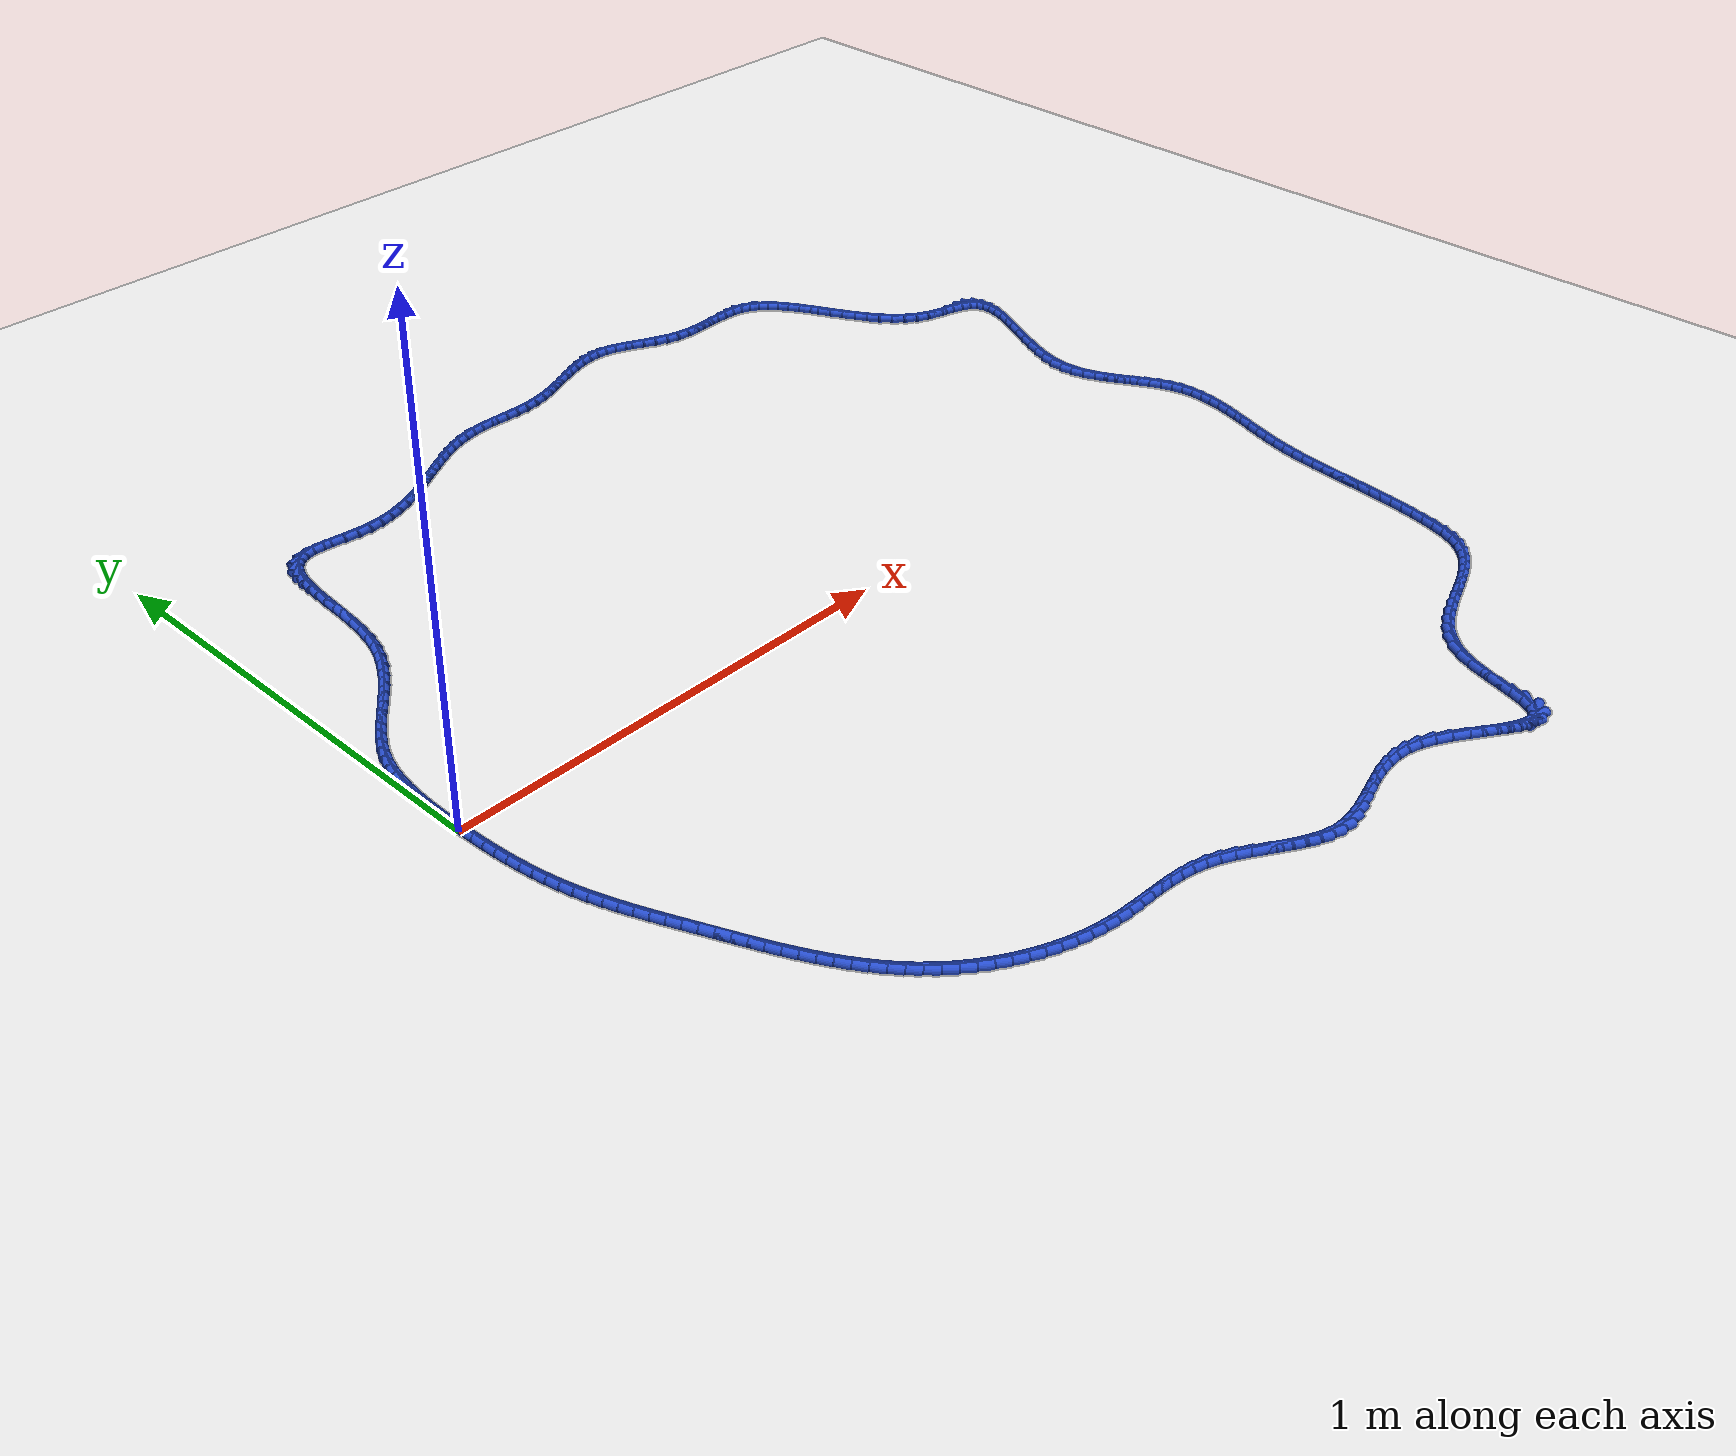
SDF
<sdf version="1.6">
 <world name="default">
  <light name="sun" type="directional">
   <pose>0 0 10 0 -0 0</pose>
   <diffuse>0.8 0.8 0.8 1</diffuse>
   <specular>0.2 0.2 0.2 1</specular>
   <attenuation>
    <range>1000</range>
    <constant>0.9</constant>
    <linear>0.01</linear>
    <quadratic>0.001</quadratic>
   </attenuation>
   <direction>-0.5 0.1 -0.9</direction>
  </light>
  <model name="ground_plane">
   <static>1</static>
   <link name="link">
    <collision name="collision">
     <geometry><plane><normal>0 0 1</normal><size>100 100</size></plane></geometry>
     <surface><friction><ode><mu>100</mu><mu2>50</mu2></ode></friction></surface>
    </collision>
    <visual name="visual">
     <cast_shadows>0</cast_shadows>
     <geometry><plane><normal>0 0 1</normal><size>100 100</size></plane></geometry>
     <material>
      <script><uri>file://media/materials/scripts/gazebo.material</uri><name>Gazebo/WhiteGlow</name></script>
     </material>
    </visual>
   </link>
  </model>
  <gravity>0 0 -9.8</gravity>
  <magnetic_field>6e-06 2.3e-05 -4.2e-05</magnetic_field>
  <atmosphere type="adiabatic"/>
  <physics name="default_physics" default="0" type="ode">
   <max_step_size>0.001</max_step_size>
   <real_time_factor>1</real_time_factor>
   <real_time_update_rate>1000</real_time_update_rate>
  </physics>
  <scene><ambient>0.4 0.4 0.4 1</ambient><background>0.7 0.7 0.7 1</background><shadows>1</shadows></scene>
  <spherical_coordinates>
   <surface_model>EARTH_WGS84</surface_model>
   <latitude_deg>0</latitude_deg>
   <longitude_deg>0</longitude_deg>
   <elevation>0</elevation>
   <heading_deg>0</heading_deg>
  </spherical_coordinates>
  <model name="line">
   <link name="link_0">
    <pose>-1.5693826446727677e-17 -1.3877787807814457e-17 0.01 0 1.57 -1.5442963593698043</pose>
    <collision name="collision">
     <geometry><cylinder><radius>0.01</radius><length>0.08</length></cylinder></geometry>
    </collision>
    <visual name="visual">
     <material>
      <script><name>Gazebo/Blue</name><uri>file://media/materials/scripts/gazebo.material</uri></script>
     </material>
     <geometry><cylinder><radius>0.01</radius><length>0.08</length></cylinder></geometry>
    </visual>
   </link>
   <link name="link_1">
    <pose>-0.0007509376700477876 0.02833067181607468 0.01 0 1.57 -1.5626476190349388</pose>
    <collision name="collision">
     <geometry><cylinder><radius>0.01</radius><length>0.08</length></cylinder></geometry>
    </collision>
    <visual name="visual">
     <material>
      <script><name>Gazebo/Blue</name><uri>file://media/materials/scripts/gazebo.material</uri></script>
     </material>
     <geometry><cylinder><radius>0.01</radius><length>0.08</length></cylinder></geometry>
    </visual>
   </link>
   <link name="link_2">
    <pose>-0.0009825066827467725 0.056747924464282895 0.01 0 1.57 1.5526250393749008</pose>
    <collision name="collision">
     <geometry><cylinder><radius>0.01</radius><length>0.08</length></cylinder></geometry>
    </collision>
    <visual name="visual">
     <material>
      <script><name>Gazebo/Blue</name><uri>file://media/materials/scripts/gazebo.material</uri></script>
     </material>
     <geometry><cylinder><radius>0.01</radius><length>0.08</length></cylinder></geometry>
    </visual>
   </link>
   <link name="link_3">
    <pose>-0.0004676212184539076 0.08507991768851372 0.01 0 1.57 1.517829657913235</pose>
    <collision name="collision">
     <geometry><cylinder><radius>0.01</radius><length>0.08</length></cylinder></geometry>
    </collision>
    <visual name="visual">
     <material>
      <script><name>Gazebo/Blue</name><uri>file://media/materials/scripts/gazebo.material</uri></script>
     </material>
     <geometry><cylinder><radius>0.01</radius><length>0.08</length></cylinder></geometry>
    </visual>
   </link>
   <link name="link_4">
    <pose>0.0010208045424738691 0.11315481123265635 0.01 0 1.57 1.4738338781834048</pose>
    <collision name="collision">
     <geometry><cylinder><radius>0.01</radius><length>0.08</length></cylinder></geometry>
    </collision>
    <visual name="visual">
     <material>
      <script><name>Gazebo/Blue</name><uri>file://media/materials/scripts/gazebo.material</uri></script>
     </material>
     <geometry><cylinder><radius>0.01</radius><length>0.08</length></cylinder></geometry>
    </visual>
   </link>
   <link name="link_5">
    <pose>0.003709856419679622 0.14080076484059975 0.01 0 1.57 1.4197378369679456</pose>
    <collision name="collision">
     <geometry><cylinder><radius>0.01</radius><length>0.08</length></cylinder></geometry>
    </collision>
    <visual name="visual">
     <material>
      <script><name>Gazebo/Blue</name><uri>file://media/materials/scripts/gazebo.material</uri></script>
     </material>
     <geometry><cylinder><radius>0.01</radius><length>0.08</length></cylinder></geometry>
    </visual>
   </link>
   <link name="link_6">
    <pose>0.007826620232806412 0.16784593825623315 0.01 0 1.57 1.354551010323729</pose>
    <collision name="collision">
     <geometry><cylinder><radius>0.01</radius><length>0.08</length></cylinder></geometry>
    </collision>
    <visual name="visual">
     <material>
      <script><name>Gazebo/Blue</name><uri>file://media/materials/scripts/gazebo.material</uri></script>
     </material>
     <geometry><cylinder><radius>0.01</radius><length>0.08</length></cylinder></geometry>
    </visual>
   </link>
   <link name="link_7">
    <pose>0.013598181801497303 0.19411849122344563 0.01 0 1.57 1.2773478894778796</pose>
    <collision name="collision">
     <geometry><cylinder><radius>0.01</radius><length>0.08</length></cylinder></geometry>
    </collision>
    <visual name="visual">
     <material>
      <script><name>Gazebo/Blue</name><uri>file://media/materials/scripts/gazebo.material</uri></script>
     </material>
     <geometry><cylinder><radius>0.01</radius><length>0.08</length></cylinder></geometry>
    </visual>
   </link>
   <link name="link_8">
    <pose>0.02125162694539536 0.21944658348612625 0.01 0 1.57 1.1875553763427937</pose>
    <collision name="collision">
     <geometry><cylinder><radius>0.01</radius><length>0.08</length></cylinder></geometry>
    </collision>
    <visual name="visual">
     <material>
      <script><name>Gazebo/Blue</name><uri>file://media/materials/scripts/gazebo.material</uri></script>
     </material>
     <geometry><cylinder><radius>0.01</radius><length>0.08</length></cylinder></geometry>
    </visual>
   </link>
   <link name="link_9">
    <pose>0.031013412464680493 0.24365882709709122 0.01 0 1.57 1.0931232626299046</pose>
    <collision name="collision">
     <geometry><cylinder><radius>0.01</radius><length>0.08</length></cylinder></geometry>
    </collision>
    <visual name="visual">
     <material>
      <script><name>Gazebo/Blue</name><uri>file://media/materials/scripts/gazebo.material</uri></script>
     </material>
     <geometry><cylinder><radius>0.01</radius><length>0.08</length></cylinder></geometry>
    </visual>
   </link>
   <link name="link_10">
    <pose>0.04294289728708785 0.2667039891501601 0.01 0 1.57 1.013885816237489</pose>
    <collision name="collision">
     <geometry><cylinder><radius>0.01</radius><length>0.08</length></cylinder></geometry>
    </collision>
    <visual name="visual">
     <material>
      <script><name>Gazebo/Blue</name><uri>file://media/materials/scripts/gazebo.material</uri></script>
     </material>
     <geometry><cylinder><radius>0.01</radius><length>0.08</length></cylinder></geometry>
    </visual>
   </link>
   <link name="link_11">
    <pose>0.0567085049656953 0.2888119465778625 0.01 0 1.57 0.9536576537914302</pose>
    <collision name="collision">
     <geometry><cylinder><radius>0.01</radius><length>0.08</length></cylinder></geometry>
    </collision>
    <visual name="visual">
     <material>
      <script><name>Gazebo/Blue</name><uri>file://media/materials/scripts/gazebo.material</uri></script>
     </material>
     <geometry><cylinder><radius>0.01</radius><length>0.08</length></cylinder></geometry>
    </visual>
   </link>
   <link name="link_12">
    <pose>0.07192283602420142 0.3102527169697327 0.01 0 1.57 0.9124707648080158</pose>
    <collision name="collision">
     <geometry><cylinder><radius>0.01</radius><length>0.08</length></cylinder></geometry>
    </collision>
    <visual name="visual">
     <material>
      <script><name>Gazebo/Blue</name><uri>file://media/materials/scripts/gazebo.material</uri></script>
     </material>
     <geometry><cylinder><radius>0.01</radius><length>0.08</length></cylinder></geometry>
    </visual>
   </link>
   <link name="link_13">
    <pose>0.08819849098630482 0.33129631791530484 0.01 0 1.57 0.8897780737212941</pose>
    <collision name="collision">
     <geometry><cylinder><radius>0.01</radius><length>0.08</length></cylinder></geometry>
    </collision>
    <visual name="visual">
     <material>
      <script><name>Gazebo/Blue</name><uri>file://media/materials/scripts/gazebo.material</uri></script>
     </material>
     <geometry><cylinder><radius>0.01</radius><length>0.08</length></cylinder></geometry>
    </visual>
   </link>
   <link name="link_14">
    <pose>0.10514807037570413 0.3522127670041131 0.01 0 1.57 0.8849031187614891</pose>
    <collision name="collision">
     <geometry><cylinder><radius>0.01</radius><length>0.08</length></cylinder></geometry>
    </collision>
    <visual name="visual">
     <material>
      <script><name>Gazebo/Blue</name><uri>file://media/materials/scripts/gazebo.material</uri></script>
     </material>
     <geometry><cylinder><radius>0.01</radius><length>0.08</length></cylinder></geometry>
    </visual>
   </link>
   <link name="link_15">
    <pose>0.12238417471609796 0.37327208182569166 0.01 0 1.57 0.8972642594297092</pose>
    <collision name="collision">
     <geometry><cylinder><radius>0.01</radius><length>0.08</length></cylinder></geometry>
    </collision>
    <visual name="visual">
     <material>
      <script><name>Gazebo/Blue</name><uri>file://media/materials/scripts/gazebo.material</uri></script>
     </material>
     <geometry><cylinder><radius>0.01</radius><length>0.08</length></cylinder></geometry>
    </visual>
   </link>
   <link name="link_16">
    <pose>0.1395194045311849 0.3947442799695746 0.01 0 1.57 0.9264109444927395</pose>
    <collision name="collision">
     <geometry><cylinder><radius>0.01</radius><length>0.08</length></cylinder></geometry>
    </collision>
    <visual name="visual">
     <material>
      <script><name>Gazebo/Blue</name><uri>file://media/materials/scripts/gazebo.material</uri></script>
     </material>
     <geometry><cylinder><radius>0.01</radius><length>0.08</length></cylinder></geometry>
    </visual>
   </link>
   <link name="link_17">
    <pose>0.1561663603446636 0.41689937902529645 0.01 0 1.57 0.9719103549272091</pose>
    <collision name="collision">
     <geometry><cylinder><radius>0.01</radius><length>0.08</length></cylinder></geometry>
    </collision>
    <visual name="visual">
     <material>
      <script><name>Gazebo/Blue</name><uri>file://media/materials/scripts/gazebo.material</uri></script>
     </material>
     <geometry><cylinder><radius>0.01</radius><length>0.08</length></cylinder></geometry>
    </visual>
   </link>
   <link name="link_18">
    <pose>0.17193764268023265 0.4400073965823911 0.01 0 1.57 1.033112112645418</pose>
    <collision name="collision">
     <geometry><cylinder><radius>0.01</radius><length>0.08</length></cylinder></geometry>
    </collision>
    <visual name="visual">
     <material>
      <script><name>Gazebo/Blue</name><uri>file://media/materials/scripts/gazebo.material</uri></script>
     </material>
     <geometry><cylinder><radius>0.01</radius><length>0.08</length></cylinder></geometry>
    </visual>
   </link>
   <link name="link_19">
    <pose>0.18644585206159064 0.46433835023039277 0.01 0 1.57 1.1088297099244484</pose>
    <collision name="collision">
     <geometry><cylinder><radius>0.01</radius><length>0.08</length></cylinder></geometry>
    </collision>
    <visual name="visual">
     <material>
      <script><name>Gazebo/Blue</name><uri>file://media/materials/scripts/gazebo.material</uri></script>
     </material>
     <geometry><cylinder><radius>0.01</radius><length>0.08</length></cylinder></geometry>
    </visual>
   </link>
   <link name="link_20">
    <pose>0.1993035890124363 0.4901622575588358 0.01 0 1.57 1.1970229695478407</pose>
    <collision name="collision">
     <geometry><cylinder><radius>0.01</radius><length>0.08</length></cylinder></geometry>
    </collision>
    <visual name="visual">
     <material>
      <script><name>Gazebo/Blue</name><uri>file://media/materials/scripts/gazebo.material</uri></script>
     </material>
     <geometry><cylinder><radius>0.01</radius><length>0.08</length></cylinder></geometry>
    </visual>
   </link>
   <link name="link_21">
    <pose>0.21012345405646815 0.5177491361572544 0.01 0 1.57 1.2937979636964438</pose>
    <collision name="collision">
     <geometry><cylinder><radius>0.01</radius><length>0.08</length></cylinder></geometry>
    </collision>
    <visual name="visual">
     <material>
      <script><name>Gazebo/Blue</name><uri>file://media/materials/scripts/gazebo.material</uri></script>
     </material>
     <geometry><cylinder><radius>0.01</radius><length>0.08</length></cylinder></geometry>
    </visual>
   </link>
   <link name="link_22">
    <pose>0.21853895741755916 0.5473491634436342 0.01 0 1.57 1.3790163676794251</pose>
    <collision name="collision">
     <geometry><cylinder><radius>0.01</radius><length>0.08</length></cylinder></geometry>
    </collision>
    <visual name="visual">
     <material>
      <script><name>Gazebo/Blue</name><uri>file://media/materials/scripts/gazebo.material</uri></script>
     </material>
     <geometry><cylinder><radius>0.01</radius><length>0.08</length></cylinder></geometry>
    </visual>
   </link>
   <link name="link_23">
    <pose>0.22464140408952282 0.5787781382129381 0.01 0 1.57 1.4390722565192233</pose>
    <collision name="collision">
     <geometry><cylinder><radius>0.01</radius><length>0.08</length></cylinder></geometry>
    </collision>
    <visual name="visual">
     <material>
      <script><name>Gazebo/Blue</name><uri>file://media/materials/scripts/gazebo.material</uri></script>
     </material>
     <geometry><cylinder><radius>0.01</radius><length>0.08</length></cylinder></geometry>
    </visual>
   </link>
   <link name="link_24">
    <pose>0.2289674018992578 0.611429333612908 0.01 0 1.57 1.4776936303249002</pose>
    <collision name="collision">
     <geometry><cylinder><radius>0.01</radius><length>0.08</length></cylinder></geometry>
    </collision>
    <visual name="visual">
     <material>
      <script><name>Gazebo/Blue</name><uri>file://media/materials/scripts/gazebo.material</uri></script>
     </material>
     <geometry><cylinder><radius>0.01</radius><length>0.08</length></cylinder></geometry>
    </visual>
   </link>
   <link name="link_25">
    <pose>0.23207196938696725 0.6446785537837316 0.01 0 1.57 1.4975401751997912</pose>
    <collision name="collision">
     <geometry><cylinder><radius>0.01</radius><length>0.08</length></cylinder></geometry>
    </collision>
    <visual name="visual">
     <material>
      <script><name>Gazebo/Blue</name><uri>file://media/materials/scripts/gazebo.material</uri></script>
     </material>
     <geometry><cylinder><radius>0.01</radius><length>0.08</length></cylinder></geometry>
    </visual>
   </link>
   <link name="link_26">
    <pose>0.23451012509285446 0.6779016028655971 0.01 0 1.57 1.4994845151319292</pose>
    <collision name="collision">
     <geometry><cylinder><radius>0.01</radius><length>0.08</length></cylinder></geometry>
    </collision>
    <visual name="visual">
     <material>
      <script><name>Gazebo/Blue</name><uri>file://media/materials/scripts/gazebo.material</uri></script>
     </material>
     <geometry><cylinder><radius>0.01</radius><length>0.08</length></cylinder></geometry>
    </visual>
   </link>
   <link name="link_27">
    <pose>0.23683688755712265 0.710474284998692 0.01 0 1.57 1.4825103139550786</pose>
    <collision name="collision">
     <geometry><cylinder><radius>0.01</radius><length>0.08</length></cylinder></geometry>
    </collision>
    <visual name="visual">
     <material>
      <script><name>Gazebo/Blue</name><uri>file://media/materials/scripts/gazebo.material</uri></script>
     </material>
     <geometry><cylinder><radius>0.01</radius><length>0.08</length></cylinder></geometry>
    </visual>
   </link>
   <link name="link_28">
    <pose>0.239607275319975 0.7417724043232042 0.01 0 1.57 1.4432906906127048</pose>
    <collision name="collision">
     <geometry><cylinder><radius>0.01</radius><length>0.08</length></cylinder></geometry>
    </collision>
    <visual name="visual">
     <material>
      <script><name>Gazebo/Blue</name><uri>file://media/materials/scripts/gazebo.material</uri></script>
     </material>
     <geometry><cylinder><radius>0.01</radius><length>0.08</length></cylinder></geometry>
    </visual>
   </link>
   <link name="link_29">
    <pose>0.243376306921615 0.7711717649793222 0.01 0 1.57 1.3752828501387808</pose>
    <collision name="collision">
     <geometry><cylinder><radius>0.01</radius><length>0.08</length></cylinder></geometry>
    </collision>
    <visual name="visual">
     <material>
      <script><name>Gazebo/Blue</name><uri>file://media/materials/scripts/gazebo.material</uri></script>
     </material>
     <geometry><cylinder><radius>0.01</radius><length>0.08</length></cylinder></geometry>
    </visual>
   </link>
   <link name="link_30">
    <pose>0.2486990009022455 0.7980481711072328 0.01 0 1.57 1.2672979643005648</pose>
    <collision name="collision">
     <geometry><cylinder><radius>0.01</radius><length>0.08</length></cylinder></geometry>
    </collision>
    <visual name="visual">
     <material>
      <script><name>Gazebo/Blue</name><uri>file://media/materials/scripts/gazebo.material</uri></script>
     </material>
     <geometry><cylinder><radius>0.01</radius><length>0.08</length></cylinder></geometry>
    </visual>
   </link>
   <link name="link_31">
    <pose>0.2561303758020701 0.821777426847125 0.01 0 1.57 1.1025049783706544</pose>
    <collision name="collision">
     <geometry><cylinder><radius>0.01</radius><length>0.08</length></cylinder></geometry>
    </collision>
    <visual name="visual">
     <material>
      <script><name>Gazebo/Blue</name><uri>file://media/materials/scripts/gazebo.material</uri></script>
     </material>
     <geometry><cylinder><radius>0.01</radius><length>0.08</length></cylinder></geometry>
    </visual>
   </link>
   <link name="link_32">
    <pose>0.26622545016129184 0.8417353363391863 0.01 0 1.57 0.8631109421613034</pose>
    <collision name="collision">
     <geometry><cylinder><radius>0.01</radius><length>0.08</length></cylinder></geometry>
    </collision>
    <visual name="visual">
     <material>
      <script><name>Gazebo/Blue</name><uri>file://media/materials/scripts/gazebo.material</uri></script>
     </material>
     <geometry><cylinder><radius>0.01</radius><length>0.08</length></cylinder></geometry>
    </visual>
   </link>
   <link name="link_33">
    <pose>0.279539242520114 0.857297703723604 0.01 0 1.57 0.5528098778946544</pose>
    <collision name="collision">
     <geometry><cylinder><radius>0.01</radius><length>0.08</length></cylinder></geometry>
    </collision>
    <visual name="visual">
     <material>
      <script><name>Gazebo/Blue</name><uri>file://media/materials/scripts/gazebo.material</uri></script>
     </material>
     <geometry><cylinder><radius>0.01</radius><length>0.08</length></cylinder></geometry>
    </visual>
   </link>
   <link name="link_34">
    <pose>0.29662677141873994 0.8678403331405669 0.01 0 1.57 0.23369263647647787</pose>
    <collision name="collision">
     <geometry><cylinder><radius>0.01</radius><length>0.08</length></cylinder></geometry>
    </collision>
    <visual name="visual">
     <material>
      <script><name>Gazebo/Blue</name><uri>file://media/materials/scripts/gazebo.material</uri></script>
     </material>
     <geometry><cylinder><radius>0.01</radius><length>0.08</length></cylinder></geometry>
    </visual>
   </link>
   <link name="link_35">
    <pose>0.31792598854462595 0.8729104377418461 0.01 0 1.57 0.022684399845467704</pose>
    <collision name="collision">
     <geometry><cylinder><radius>0.01</radius><length>0.08</length></cylinder></geometry>
    </collision>
    <visual name="visual">
     <material>
      <script><name>Gazebo/Blue</name><uri>file://media/materials/scripts/gazebo.material</uri></script>
     </material>
     <geometry><cylinder><radius>0.01</radius><length>0.08</length></cylinder></geometry>
    </visual>
   </link>
   <link name="link_36">
    <pose>0.342903727188701 0.8734771399607384 0.01 0 1.57 -0.0817232055964169</pose>
    <collision name="collision">
     <geometry><cylinder><radius>0.01</radius><length>0.08</length></cylinder></geometry>
    </collision>
    <visual name="visual">
     <material>
      <script><name>Gazebo/Blue</name><uri>file://media/materials/scripts/gazebo.material</uri></script>
     </material>
     <geometry><cylinder><radius>0.01</radius><length>0.08</length></cylinder></geometry>
    </visual>
   </link>
   <link name="link_37">
    <pose>0.3705463591314357 0.8712130528487595 0.01 0 1.57 -0.11614263825957945</pose>
    <collision name="collision">
     <geometry><cylinder><radius>0.01</radius><length>0.08</length></cylinder></geometry>
    </collision>
    <visual name="visual">
     <material>
      <script><name>Gazebo/Blue</name><uri>file://media/materials/scripts/gazebo.material</uri></script>
     </material>
     <geometry><cylinder><radius>0.01</radius><length>0.08</length></cylinder></geometry>
    </visual>
   </link>
   <link name="link_38">
    <pose>0.39983683356402916 0.8677958008046194 0.01 0 1.57 -0.096380606063075</pose>
    <collision name="collision">
     <geometry><cylinder><radius>0.01</radius><length>0.08</length></cylinder></geometry>
    </collision>
    <visual name="visual">
     <material>
      <script><name>Gazebo/Blue</name><uri>file://media/materials/scripts/gazebo.material</uri></script>
     </material>
     <geometry><cylinder><radius>0.01</radius><length>0.08</length></cylinder></geometry>
    </visual>
   </link>
   <link name="link_39">
    <pose>0.42975809967767986 0.8649030082270286 0.01 0 1.57 -0.02363803837802374</pose>
    <collision name="collision">
     <geometry><cylinder><radius>0.01</radius><length>0.08</length></cylinder></geometry>
    </collision>
    <visual name="visual">
     <material>
      <script><name>Gazebo/Blue</name><uri>file://media/materials/scripts/gazebo.material</uri></script>
     </material>
     <geometry><cylinder><radius>0.01</radius><length>0.08</length></cylinder></geometry>
    </visual>
   </link>
   <link name="link_40">
    <pose>0.45929727903754886 0.8642046298922577 0.01 0 1.57 0.08625943504643795</pose>
    <collision name="collision">
     <geometry><cylinder><radius>0.01</radius><length>0.08</length></cylinder></geometry>
    </collision>
    <visual name="visual">
     <material>
      <script><name>Gazebo/Blue</name><uri>file://media/materials/scripts/gazebo.material</uri></script>
     </material>
     <geometry><cylinder><radius>0.01</radius><length>0.08</length></cylinder></geometry>
    </visual>
   </link>
   <link name="link_41">
    <pose>0.48782194758707875 0.8666712725643752 0.01 0 1.57 0.19183564733399788</pose>
    <collision name="collision">
     <geometry><cylinder><radius>0.01</radius><length>0.08</length></cylinder></geometry>
    </collision>
    <visual name="visual">
     <material>
      <script><name>Gazebo/Blue</name><uri>file://media/materials/scripts/gazebo.material</uri></script>
     </material>
     <geometry><cylinder><radius>0.01</radius><length>0.08</length></cylinder></geometry>
    </visual>
   </link>
   <link name="link_42">
    <pose>0.5153796445882639 0.8720236402008416 0.01 0 1.57 0.28514573068680454</pose>
    <collision name="collision">
     <geometry><cylinder><radius>0.01</radius><length>0.08</length></cylinder></geometry>
    </collision>
    <visual name="visual">
     <material>
      <script><name>Gazebo/Blue</name><uri>file://media/materials/scripts/gazebo.material</uri></script>
     </material>
     <geometry><cylinder><radius>0.01</radius><length>0.08</length></cylinder></geometry>
    </visual>
   </link>
   <link name="link_43">
    <pose>0.5420883910280179 0.8798528778499993 0.01 0 1.57 0.36401060627234266</pose>
    <collision name="collision">
     <geometry><cylinder><radius>0.01</radius><length>0.08</length></cylinder></geometry>
    </collision>
    <visual name="visual">
     <material>
      <script><name>Gazebo/Blue</name><uri>file://media/materials/scripts/gazebo.material</uri></script>
     </material>
     <geometry><cylinder><radius>0.01</radius><length>0.08</length></cylinder></geometry>
    </visual>
   </link>
   <link name="link_44">
    <pose>0.5680662078932549 0.8897501305601909 0.01 0 1.57 0.4275063619447899</pose>
    <collision name="collision">
     <geometry><cylinder><radius>0.01</radius><length>0.08</length></cylinder></geometry>
    </collision>
    <visual name="visual">
     <material>
      <script><name>Gazebo/Blue</name><uri>file://media/materials/scripts/gazebo.material</uri></script>
     </material>
     <geometry><cylinder><radius>0.01</radius><length>0.08</length></cylinder></geometry>
    </visual>
   </link>
   <link name="link_45">
    <pose>0.5934311161708884 0.9013065433797589 0.01 0 1.57 0.47553280146876165</pose>
    <collision name="collision">
     <geometry><cylinder><radius>0.01</radius><length>0.08</length></cylinder></geometry>
    </collision>
    <visual name="visual">
     <material>
      <script><name>Gazebo/Blue</name><uri>file://media/materials/scripts/gazebo.material</uri></script>
     </material>
     <geometry><cylinder><radius>0.01</radius><length>0.08</length></cylinder></geometry>
    </visual>
   </link>
   <link name="link_46">
    <pose>0.6183011368478332 0.9141132613570462 0.01 0 1.57 0.5083723859201813</pose>
    <collision name="collision">
     <geometry><cylinder><radius>0.01</radius><length>0.08</length></cylinder></geometry>
    </collision>
    <visual name="visual">
     <material>
      <script><name>Gazebo/Blue</name><uri>file://media/materials/scripts/gazebo.material</uri></script>
     </material>
     <geometry><cylinder><radius>0.01</radius><length>0.08</length></cylinder></geometry>
    </visual>
   </link>
   <link name="link_47">
    <pose>0.6427942909110029 0.9277614295403946 0.01 0 1.57 0.5263511903529184</pose>
    <collision name="collision">
     <geometry><cylinder><radius>0.01</radius><length>0.08</length></cylinder></geometry>
    </collision>
    <visual name="visual">
     <material>
      <script><name>Gazebo/Blue</name><uri>file://media/materials/scripts/gazebo.material</uri></script>
     </material>
     <geometry><cylinder><radius>0.01</radius><length>0.08</length></cylinder></geometry>
    </visual>
   </link>
   <link name="link_48">
    <pose>0.6670285993473112 0.9418421929781471 0.01 0 1.57 0.5296205427475181</pose>
    <collision name="collision">
     <geometry><cylinder><radius>0.01</radius><length>0.08</length></cylinder></geometry>
    </collision>
    <visual name="visual">
     <material>
      <script><name>Gazebo/Blue</name><uri>file://media/materials/scripts/gazebo.material</uri></script>
     </material>
     <geometry><cylinder><radius>0.01</radius><length>0.08</length></cylinder></geometry>
    </visual>
   </link>
   <link name="link_49">
    <pose>0.6911220831436723 0.9559466967186456 0.01 0 1.57 0.5180403513013273</pose>
    <collision name="collision">
     <geometry><cylinder><radius>0.01</radius><length>0.08</length></cylinder></geometry>
    </collision>
    <visual name="visual">
     <material>
      <script><name>Gazebo/Blue</name><uri>file://media/materials/scripts/gazebo.material</uri></script>
     </material>
     <geometry><cylinder><radius>0.01</radius><length>0.08</length></cylinder></geometry>
    </visual>
   </link>
   <link name="link_50">
    <pose>0.7151927632870003 0.9696660858102333 0.01 0 1.57 0.49114668452280724</pose>
    <collision name="collision">
     <geometry><cylinder><radius>0.01</radius><length>0.08</length></cylinder></geometry>
    </collision>
    <visual name="visual">
     <material>
      <script><name>Gazebo/Blue</name><uri>file://media/materials/scripts/gazebo.material</uri></script>
     </material>
     <geometry><cylinder><radius>0.01</radius><length>0.08</length></cylinder></geometry>
    </visual>
   </link>
   <link name="link_51">
    <pose>0.7393586607642093 0.9825915053012524 0.01 0 1.57 0.448206829963109</pose>
    <collision name="collision">
     <geometry><cylinder><radius>0.01</radius><length>0.08</length></cylinder></geometry>
    </collision>
    <visual name="visual">
     <material>
      <script><name>Gazebo/Blue</name><uri>file://media/materials/scripts/gazebo.material</uri></script>
     </material>
     <geometry><cylinder><radius>0.01</radius><length>0.08</length></cylinder></geometry>
    </visual>
   </link>
   <link name="link_52">
    <pose>0.7637377965622126 0.994314100240045 0.01 0 1.57 0.38839212132353085</pose>
    <collision name="collision">
     <geometry><cylinder><radius>0.01</radius><length>0.08</length></cylinder></geometry>
    </collision>
    <visual name="visual">
     <material>
      <script><name>Gazebo/Blue</name><uri>file://media/materials/scripts/gazebo.material</uri></script>
     </material>
     <geometry><cylinder><radius>0.01</radius><length>0.08</length></cylinder></geometry>
    </visual>
   </link>
   <link name="link_53">
    <pose>0.7884481916679248 1.004425015674954 0.01 0 1.57 0.31111868547416</pose>
    <collision name="collision">
     <geometry><cylinder><radius>0.01</radius><length>0.08</length></cylinder></geometry>
    </collision>
    <visual name="visual">
     <material>
      <script><name>Gazebo/Blue</name><uri>file://media/materials/scripts/gazebo.material</uri></script>
     </material>
     <geometry><cylinder><radius>0.01</radius><length>0.08</length></cylinder></geometry>
    </visual>
   </link>
   <link name="link_54">
    <pose>0.81360786706826 1.012515396654322 0.01 0 1.57 0.21659275194439018</pose>
    <collision name="collision">
     <geometry><cylinder><radius>0.01</radius><length>0.08</length></cylinder></geometry>
    </collision>
    <visual name="visual">
     <material>
      <script><name>Gazebo/Blue</name><uri>file://media/materials/scripts/gazebo.material</uri></script>
     </material>
     <geometry><cylinder><radius>0.01</radius><length>0.08</length></cylinder></geometry>
    </visual>
   </link>
   <link name="link_55">
    <pose>0.839334826599655 1.0181764726476783 0.01 0 1.57 0.11613499731957339</pose>
    <collision name="collision">
     <geometry><cylinder><radius>0.01</radius><length>0.08</length></cylinder></geometry>
    </collision>
    <visual name="visual">
     <material>
      <script><name>Gazebo/Blue</name><uri>file://media/materials/scripts/gazebo.material</uri></script>
     </material>
     <geometry><cylinder><radius>0.01</radius><length>0.08</length></cylinder></geometry>
    </visual>
   </link>
   <link name="link_56">
    <pose>0.8656958240897653 1.0212517452144667 0.01 0 1.57 0.04238606104450635</pose>
    <collision name="collision">
     <geometry><cylinder><radius>0.01</radius><length>0.08</length></cylinder></geometry>
    </collision>
    <visual name="visual">
     <material>
      <script><name>Gazebo/Blue</name><uri>file://media/materials/scripts/gazebo.material</uri></script>
     </material>
     <geometry><cylinder><radius>0.01</radius><length>0.08</length></cylinder></geometry>
    </visual>
   </link>
   <link name="link_57">
    <pose>0.8925935059429149 1.0223925152421307 0.01 0 1.57 0.0006929504338573164</pose>
    <collision name="collision">
     <geometry><cylinder><radius>0.01</radius><length>0.08</length></cylinder></geometry>
    </collision>
    <visual name="visual">
     <material>
      <script><name>Gazebo/Blue</name><uri>file://media/materials/scripts/gazebo.material</uri></script>
     </material>
     <geometry><cylinder><radius>0.01</radius><length>0.08</length></cylinder></geometry>
    </visual>
   </link>
   <link name="link_58">
    <pose>0.9198977392856119 1.0224114357255 0.01 0 1.57 -0.010524238132485623</pose>
    <collision name="collision">
     <geometry><cylinder><radius>0.01</radius><length>0.08</length></cylinder></geometry>
    </collision>
    <visual name="visual">
     <material>
      <script><name>Gazebo/Blue</name><uri>file://media/materials/scripts/gazebo.material</uri></script>
     </material>
     <geometry><cylinder><radius>0.01</radius><length>0.08</length></cylinder></geometry>
    </visual>
   </link>
   <link name="link_59">
    <pose>0.9474783912443645 1.0221211596594053 0.01 0 1.57 0.007688414099824325</pose>
    <collision name="collision">
     <geometry><cylinder><radius>0.01</radius><length>0.08</length></cylinder></geometry>
    </collision>
    <visual name="visual">
     <material>
      <script><name>Gazebo/Blue</name><uri>file://media/materials/scripts/gazebo.material</uri></script>
     </material>
     <geometry><cylinder><radius>0.01</radius><length>0.08</length></cylinder></geometry>
    </visual>
   </link>
   <link name="link_60">
    <pose>0.9752053289456803 1.0223343400386753 0.01 0 1.57 0.05506753761496748</pose>
    <collision name="collision">
     <geometry><cylinder><radius>0.01</radius><length>0.08</length></cylinder></geometry>
    </collision>
    <visual name="visual">
     <material>
      <script><name>Gazebo/Blue</name><uri>file://media/materials/scripts/gazebo.material</uri></script>
     </material>
     <geometry><cylinder><radius>0.01</radius><length>0.08</length></cylinder></geometry>
    </visual>
   </link>
   <link name="link_61">
    <pose>1.0029484195160674 1.023863629858141 0.01 0 1.57 0.13163289645221124</pose>
    <collision name="collision">
     <geometry><cylinder><radius>0.01</radius><length>0.08</length></cylinder></geometry>
    </collision>
    <visual name="visual">
     <material>
      <script><name>Gazebo/Blue</name><uri>file://media/materials/scripts/gazebo.material</uri></script>
     </material>
     <geometry><cylinder><radius>0.01</radius><length>0.08</length></cylinder></geometry>
    </visual>
   </link>
   <link name="link_62">
    <pose>1.0305775300820341 1.0275216821126314 0.01 0 1.57 0.22777655111118578</pose>
    <collision name="collision">
     <geometry><cylinder><radius>0.01</radius><length>0.08</length></cylinder></geometry>
    </collision>
    <visual name="visual">
     <material>
      <script><name>Gazebo/Blue</name><uri>file://media/materials/scripts/gazebo.material</uri></script>
     </material>
     <geometry><cylinder><radius>0.01</radius><length>0.08</length></cylinder></geometry>
    </visual>
   </link>
   <link name="link_63">
    <pose>1.0579828833005853 1.033874221984532 0.01 0 1.57 0.3050537521665217</pose>
    <collision name="collision">
     <geometry><cylinder><radius>0.01</radius><length>0.08</length></cylinder></geometry>
    </collision>
    <visual name="visual">
     <material>
      <script><name>Gazebo/Blue</name><uri>file://media/materials/scripts/gazebo.material</uri></script>
     </material>
     <geometry><cylinder><radius>0.01</radius><length>0.08</length></cylinder></geometry>
    </visual>
   </link>
   <link name="link_64">
    <pose>1.0851421474589071 1.0424261937460781 0.01 0 1.57 0.35481304464475105</pose>
    <collision name="collision">
     <geometry><cylinder><radius>0.01</radius><length>0.08</length></cylinder></geometry>
    </collision>
    <visual name="visual">
     <material>
      <script><name>Gazebo/Blue</name><uri>file://media/materials/scripts/gazebo.material</uri></script>
     </material>
     <geometry><cylinder><radius>0.01</radius><length>0.08</length></cylinder></geometry>
    </visual>
   </link>
   <link name="link_65">
    <pose>1.1120564678859914 1.052397747589743 0.01 0 1.57 0.37866499751781546</pose>
    <collision name="collision">
     <geometry><cylinder><radius>0.01</radius><length>0.08</length></cylinder></geometry>
    </collision>
    <visual name="visual">
     <material>
      <script><name>Gazebo/Blue</name><uri>file://media/materials/scripts/gazebo.material</uri></script>
     </material>
     <geometry><cylinder><radius>0.01</radius><length>0.08</length></cylinder></geometry>
    </visual>
   </link>
   <link name="link_66">
    <pose>1.138726990205139 1.0630090301378254 0.01 0 1.57 0.37724048293892326</pose>
    <collision name="collision">
     <geometry><cylinder><radius>0.01</radius><length>0.08</length></cylinder></geometry>
    </collision>
    <visual name="visual">
     <material>
      <script><name>Gazebo/Blue</name><uri>file://media/materials/scripts/gazebo.material</uri></script>
     </material>
     <geometry><cylinder><radius>0.01</radius><length>0.08</length></cylinder></geometry>
    </visual>
   </link>
   <link name="link_67">
    <pose>1.165154860039651 1.073480188012624 0.01 0 1.57 0.3497442495089448</pose>
    <collision name="collision">
     <geometry><cylinder><radius>0.01</radius><length>0.08</length></cylinder></geometry>
    </collision>
    <visual name="visual">
     <material>
      <script><name>Gazebo/Blue</name><uri>file://media/materials/scripts/gazebo.material</uri></script>
     </material>
     <geometry><cylinder><radius>0.01</radius><length>0.08</length></cylinder></geometry>
    </visual>
   </link>
   <link name="link_68">
    <pose>1.1913412230128269 1.0830313678364363 0.01 0 1.57 0.2938435220388938</pose>
    <collision name="collision">
     <geometry><cylinder><radius>0.01</radius><length>0.08</length></cylinder></geometry>
    </collision>
    <visual name="visual">
     <material>
      <script><name>Gazebo/Blue</name><uri>file://media/materials/scripts/gazebo.material</uri></script>
     </material>
     <geometry><cylinder><radius>0.01</radius><length>0.08</length></cylinder></geometry>
    </visual>
   </link>
   <link name="link_69">
    <pose>1.2172872247479678 1.0908827162315615 0.01 0 1.57 0.20599492752507853</pose>
    <collision name="collision">
     <geometry><cylinder><radius>0.01</radius><length>0.08</length></cylinder></geometry>
    </collision>
    <visual name="visual">
     <material>
      <script><name>Gazebo/Blue</name><uri>file://media/materials/scripts/gazebo.material</uri></script>
     </material>
     <geometry><cylinder><radius>0.01</radius><length>0.08</length></cylinder></geometry>
    </visual>
   </link>
   <link name="link_70">
    <pose>1.2429940108683744 1.096254379820298 0.01 0 1.57 0.08274085306119316</pose>
    <collision name="collision">
     <geometry><cylinder><radius>0.01</radius><length>0.08</length></cylinder></geometry>
    </collision>
    <visual name="visual">
     <material>
      <script><name>Gazebo/Blue</name><uri>file://media/materials/scripts/gazebo.material</uri></script>
     </material>
     <geometry><cylinder><radius>0.01</radius><length>0.08</length></cylinder></geometry>
    </visual>
   </link>
   <link name="link_71">
    <pose>1.2684627269973467 1.098366505224944 0.01 0 1.57 -0.07560550291243678</pose>
    <collision name="collision">
     <geometry><cylinder><radius>0.01</radius><length>0.08</length></cylinder></geometry>
    </collision>
    <visual name="visual">
     <material>
      <script><name>Gazebo/Blue</name><uri>file://media/materials/scripts/gazebo.material</uri></script>
     </material>
     <geometry><cylinder><radius>0.01</radius><length>0.08</length></cylinder></geometry>
    </visual>
   </link>
   <link name="link_72">
    <pose>1.2936958692449991 1.0964550974352547 0.01 0 1.57 -0.23305854706992238</pose>
    <collision name="collision">
     <geometry><cylinder><radius>0.01</radius><length>0.08</length></cylinder></geometry>
    </collision>
    <visual name="visual">
     <material>
      <script><name>Gazebo/Blue</name><uri>file://media/materials/scripts/gazebo.material</uri></script>
     </material>
     <geometry><cylinder><radius>0.01</radius><length>0.08</length></cylinder></geometry>
    </visual>
   </link>
   <link name="link_73">
    <pose>1.3187597582667343 1.090505634209806 0.01 0 1.57 -0.34291234143875676</pose>
    <collision name="collision">
     <geometry><cylinder><radius>0.01</radius><length>0.08</length></cylinder></geometry>
    </collision>
    <visual name="visual">
     <material>
      <script><name>Gazebo/Blue</name><uri>file://media/materials/scripts/gazebo.material</uri></script>
     </material>
     <geometry><cylinder><radius>0.01</radius><length>0.08</length></cylinder></geometry>
    </visual>
   </link>
   <link name="link_74">
    <pose>1.3438108452557092 1.0815619695695144 0.01 0 1.57 -0.4053407303330899</pose>
    <collision name="collision">
     <geometry><cylinder><radius>0.01</radius><length>0.08</length></cylinder></geometry>
    </collision>
    <visual name="visual">
     <material>
      <script><name>Gazebo/Blue</name><uri>file://media/materials/scripts/gazebo.material</uri></script>
     </material>
     <geometry><cylinder><radius>0.01</radius><length>0.08</length></cylinder></geometry>
    </visual>
   </link>
   <link name="link_75">
    <pose>1.3690123903224523 1.0707479126392834 0.01 0 1.57 -0.42541830560017085</pose>
    <collision name="collision">
     <geometry><cylinder><radius>0.01</radius><length>0.08</length></cylinder></geometry>
    </collision>
    <visual name="visual">
     <material>
      <script><name>Gazebo/Blue</name><uri>file://media/materials/scripts/gazebo.material</uri></script>
     </material>
     <geometry><cylinder><radius>0.01</radius><length>0.08</length></cylinder></geometry>
    </visual>
   </link>
   <link name="link_76">
    <pose>1.3945276535774909 1.0591872725440155 0.01 0 1.57 -0.40631721493932077</pose>
    <collision name="collision">
     <geometry><cylinder><radius>0.01</radius><length>0.08</length></cylinder></geometry>
    </collision>
    <visual name="visual">
     <material>
      <script><name>Gazebo/Blue</name><uri>file://media/materials/scripts/gazebo.material</uri></script>
     </material>
     <geometry><cylinder><radius>0.01</radius><length>0.08</length></cylinder></geometry>
    </visual>
   </link>
   <link name="link_77">
    <pose>1.4205198951313547 1.0480038584086142 0.01 0 1.57 -0.3486993989973237</pose>
    <collision name="collision">
     <geometry><cylinder><radius>0.01</radius><length>0.08</length></cylinder></geometry>
    </collision>
    <visual name="visual">
     <material>
      <script><name>Gazebo/Blue</name><uri>file://media/materials/scripts/gazebo.material</uri></script>
     </material>
     <geometry><cylinder><radius>0.01</radius><length>0.08</length></cylinder></geometry>
    </visual>
   </link>
   <link name="link_78">
    <pose>1.447152375094573 1.038321479357983 0.01 0 1.57 -0.2517777966263909</pose>
    <collision name="collision">
     <geometry><cylinder><radius>0.01</radius><length>0.08</length></cylinder></geometry>
    </collision>
    <visual name="visual">
     <material>
      <script><name>Gazebo/Blue</name><uri>file://media/materials/scripts/gazebo.material</uri></script>
     </material>
     <geometry><cylinder><radius>0.01</radius><length>0.08</length></cylinder></geometry>
    </visual>
   </link>
   <link name="link_79">
    <pose>1.4745883535776731 1.0312639445170246 0.01 0 1.57 -0.12703171204883207</pose>
    <collision name="collision">
     <geometry><cylinder><radius>0.01</radius><length>0.08</length></cylinder></geometry>
    </collision>
    <visual name="visual">
     <material>
      <script><name>Gazebo/Blue</name><uri>file://media/materials/scripts/gazebo.material</uri></script>
     </material>
     <geometry><cylinder><radius>0.01</radius><length>0.08</length></cylinder></geometry>
    </visual>
   </link>
   <link name="link_80">
    <pose>1.502905263973249 1.0276473240801016 0.01 0 1.57 -0.0291010294444684</pose>
    <collision name="collision">
     <geometry><cylinder><radius>0.01</radius><length>0.08</length></cylinder></geometry>
    </collision>
    <visual name="visual">
     <material>
      <script><name>Gazebo/Blue</name><uri>file://media/materials/scripts/gazebo.material</uri></script>
     </material>
     <geometry><cylinder><radius>0.01</radius><length>0.08</length></cylinder></geometry>
    </visual>
   </link>
   <link name="link_81">
    <pose>1.5317676290393791 1.0268071623618564 0.01 0 1.57 0.02856599894414402</pose>
    <collision name="collision">
     <geometry><cylinder><radius>0.01</radius><length>0.08</length></cylinder></geometry>
    </collision>
    <visual name="visual">
     <material>
      <script><name>Gazebo/Blue</name><uri>file://media/materials/scripts/gazebo.material</uri></script>
     </material>
     <geometry><cylinder><radius>0.01</radius><length>0.08</length></cylinder></geometry>
    </visual>
   </link>
   <link name="link_82">
    <pose>1.5607159531090673 1.0276343251616813 0.01 0 1.57 0.048440760838067816</pose>
    <collision name="collision">
     <geometry><cylinder><radius>0.01</radius><length>0.08</length></cylinder></geometry>
    </collision>
    <visual name="visual">
     <material>
      <script><name>Gazebo/Blue</name><uri>file://media/materials/scripts/gazebo.material</uri></script>
     </material>
     <geometry><cylinder><radius>0.01</radius><length>0.08</length></cylinder></geometry>
    </visual>
   </link>
   <link name="link_83">
    <pose>1.5892907164868906 1.029019592123024 0.01 0 1.57 0.030059442088332652</pose>
    <collision name="collision">
     <geometry><cylinder><radius>0.01</radius><length>0.08</length></cylinder></geometry>
    </collision>
    <visual name="visual">
     <material>
      <script><name>Gazebo/Blue</name><uri>file://media/materials/scripts/gazebo.material</uri></script>
     </material>
     <geometry><cylinder><radius>0.01</radius><length>0.08</length></cylinder></geometry>
    </visual>
   </link>
   <link name="link_84">
    <pose>1.6170323994774265 1.029853742889332 0.01 0 1.57 -0.031226686805588197</pose>
    <collision name="collision">
     <geometry><cylinder><radius>0.01</radius><length>0.08</length></cylinder></geometry>
    </collision>
    <visual name="visual">
     <material>
      <script><name>Gazebo/Blue</name><uri>file://media/materials/scripts/gazebo.material</uri></script>
     </material>
     <geometry><cylinder><radius>0.01</radius><length>0.08</length></cylinder></geometry>
    </visual>
   </link>
   <link name="link_85">
    <pose>1.6434814823852517 1.0290275571040521 0.01 0 1.57 -0.1445786580720184</pose>
    <collision name="collision">
     <geometry><cylinder><radius>0.01</radius><length>0.08</length></cylinder></geometry>
    </collision>
    <visual name="visual">
     <material>
      <script><name>Gazebo/Blue</name><uri>file://media/materials/scripts/gazebo.material</uri></script>
     </material>
     <geometry><cylinder><radius>0.01</radius><length>0.08</length></cylinder></geometry>
    </visual>
   </link>
   <link name="link_86">
    <pose>1.6681784455149455 1.025431814410633 0.01 0 1.57 -0.3197570827578688</pose>
    <collision name="collision">
     <geometry><cylinder><radius>0.01</radius><length>0.08</length></cylinder></geometry>
    </collision>
    <visual name="visual">
     <material>
      <script><name>Gazebo/Blue</name><uri>file://media/materials/scripts/gazebo.material</uri></script>
     </material>
     <geometry><cylinder><radius>0.01</radius><length>0.08</length></cylinder></geometry>
    </visual>
   </link>
   <link name="link_87">
    <pose>1.690676089256236 1.0179823983774348 0.01 0 1.57 -0.5231003927801936</pose>
    <collision name="collision">
     <geometry><cylinder><radius>0.01</radius><length>0.08</length></cylinder></geometry>
    </collision>
    <visual name="visual">
     <material>
      <script><name>Gazebo/Blue</name><uri>file://media/materials/scripts/gazebo.material</uri></script>
     </material>
     <geometry><cylinder><radius>0.01</radius><length>0.08</length></cylinder></geometry>
    </visual>
   </link>
   <link name="link_88">
    <pose>1.710886518966464 1.0063273275228588 0.01 0 1.57 -0.7005459771363823</pose>
    <collision name="collision">
     <geometry><cylinder><radius>0.01</radius><length>0.08</length></cylinder></geometry>
    </collision>
    <visual name="visual">
     <material>
      <script><name>Gazebo/Blue</name><uri>file://media/materials/scripts/gazebo.material</uri></script>
     </material>
     <geometry><cylinder><radius>0.01</radius><length>0.08</length></cylinder></geometry>
    </visual>
   </link>
   <link name="link_89">
    <pose>1.7291292072505733 0.9909446890433388 0.01 0 1.57 -0.8413262260866109</pose>
    <collision name="collision">
     <geometry><cylinder><radius>0.01</radius><length>0.08</length></cylinder></geometry>
    </collision>
    <visual name="visual">
     <material>
      <script><name>Gazebo/Blue</name><uri>file://media/materials/scripts/gazebo.material</uri></script>
     </material>
     <geometry><cylinder><radius>0.01</radius><length>0.08</length></cylinder></geometry>
    </visual>
   </link>
   <link name="link_90">
    <pose>1.745745606772837 0.9723573576308594 0.01 0 1.57 -0.9462230775507207</pose>
    <collision name="collision">
     <geometry><cylinder><radius>0.01</radius><length>0.08</length></cylinder></geometry>
    </collision>
    <visual name="visual">
     <material>
      <script><name>Gazebo/Blue</name><uri>file://media/materials/scripts/gazebo.material</uri></script>
     </material>
     <geometry><cylinder><radius>0.01</radius><length>0.08</length></cylinder></geometry>
    </visual>
   </link>
   <link name="link_91">
    <pose>1.7610771701975276 0.9510882079774037 0.01 0 1.57 -1.0200430171079875</pose>
    <collision name="collision">
     <geometry><cylinder><radius>0.01</radius><length>0.08</length></cylinder></geometry>
    </collision>
    <visual name="visual">
     <material>
      <script><name>Gazebo/Blue</name><uri>file://media/materials/scripts/gazebo.material</uri></script>
     </material>
     <geometry><cylinder><radius>0.01</radius><length>0.08</length></cylinder></geometry>
    </visual>
   </link>
   <link name="link_92">
    <pose>1.7754653501889182 0.927660114774957 0.01 0 1.57 -1.0679237073010976</pose>
    <collision name="collision">
     <geometry><cylinder><radius>0.01</radius><length>0.08</length></cylinder></geometry>
    </collision>
    <visual name="visual">
     <material>
      <script><name>Gazebo/Blue</name><uri>file://media/materials/scripts/gazebo.material</uri></script>
     </material>
     <geometry><cylinder><radius>0.01</radius><length>0.08</length></cylinder></geometry>
    </visual>
   </link>
   <link name="link_93">
    <pose>1.7892515994112812 0.9025959527155033 0.01 0 1.57 -1.0938802251871629</pose>
    <collision name="collision">
     <geometry><cylinder><radius>0.01</radius><length>0.08</length></cylinder></geometry>
    </collision>
    <visual name="visual">
     <material>
      <script><name>Gazebo/Blue</name><uri>file://media/materials/scripts/gazebo.material</uri></script>
     </material>
     <geometry><cylinder><radius>0.01</radius><length>0.08</length></cylinder></geometry>
    </visual>
   </link>
   <link name="link_94">
    <pose>1.8027773705288894 0.8764185964910257 0.01 0 1.57 -1.1005089325530106</pose>
    <collision name="collision">
     <geometry><cylinder><radius>0.01</radius><length>0.08</length></cylinder></geometry>
    </collision>
    <visual name="visual">
     <material>
      <script><name>Gazebo/Blue</name><uri>file://media/materials/scripts/gazebo.material</uri></script>
     </material>
     <geometry><cylinder><radius>0.01</radius><length>0.08</length></cylinder></geometry>
    </visual>
   </link>
   <link name="link_95">
    <pose>1.816384116206015 0.8496509207935095 0.01 0 1.57 -1.089082206369195</pose>
    <collision name="collision">
     <geometry><cylinder><radius>0.01</radius><length>0.08</length></cylinder></geometry>
    </collision>
    <visual name="visual">
     <material>
      <script><name>Gazebo/Blue</name><uri>file://media/materials/scripts/gazebo.material</uri></script>
     </material>
     <geometry><cylinder><radius>0.01</radius><length>0.08</length></cylinder></geometry>
    </visual>
   </link>
   <link name="link_96">
    <pose>1.8304132891069316 0.822815800314938 0.01 0 1.57 -1.0597187426316854</pose>
    <collision name="collision">
     <geometry><cylinder><radius>0.01</radius><length>0.08</length></cylinder></geometry>
    </collision>
    <visual name="visual">
     <material>
      <script><name>Gazebo/Blue</name><uri>file://media/materials/scripts/gazebo.material</uri></script>
     </material>
     <geometry><cylinder><radius>0.01</radius><length>0.08</length></cylinder></geometry>
    </visual>
   </link>
   <link name="link_97">
    <pose>1.84520634189591 0.7964361097472953 0.01 0 1.57 -1.011559760084021</pose>
    <collision name="collision">
     <geometry><cylinder><radius>0.01</radius><length>0.08</length></cylinder></geometry>
    </collision>
    <visual name="visual">
     <material>
      <script><name>Gazebo/Blue</name><uri>file://media/materials/scripts/gazebo.material</uri></script>
     </material>
     <geometry><cylinder><radius>0.01</radius><length>0.08</length></cylinder></geometry>
    </visual>
   </link>
   <link name="link_98">
    <pose>1.8611047272372248 0.7710347237825659 0.01 0 1.57 -0.9430077917573585</pose>
    <collision name="collision">
     <geometry><cylinder><radius>0.01</radius><length>0.08</length></cylinder></geometry>
    </collision>
    <visual name="visual">
     <material>
      <script><name>Gazebo/Blue</name><uri>file://media/materials/scripts/gazebo.material</uri></script>
     </material>
     <geometry><cylinder><radius>0.01</radius><length>0.08</length></cylinder></geometry>
    </visual>
   </link>
   <link name="link_99">
    <pose>1.8784498977951483 0.7471345171127335 0.01 0 1.57 -0.8521793154982317</pose>
    <collision name="collision">
     <geometry><cylinder><radius>0.01</radius><length>0.08</length></cylinder></geometry>
    </collision>
    <visual name="visual">
     <material>
      <script><name>Gazebo/Blue</name><uri>file://media/materials/scripts/gazebo.material</uri></script>
     </material>
     <geometry><cylinder><radius>0.01</radius><length>0.08</length></cylinder></geometry>
    </visual>
   </link>
   <link name="link_100">
    <pose>1.897583306233952 0.7252583644297826 0.01 0 1.57 -0.737792761198436</pose>
    <collision name="collision">
     <geometry><cylinder><radius>0.01</radius><length>0.08</length></cylinder></geometry>
    </collision>
    <visual name="visual">
     <material>
      <script><name>Gazebo/Blue</name><uri>file://media/materials/scripts/gazebo.material</uri></script>
     </material>
     <geometry><cylinder><radius>0.01</radius><length>0.08</length></cylinder></geometry>
    </visual>
   </link>
   <link name="link_101">
    <pose>1.9188464052179102 0.7059291404256971 0.01 0 1.57 -0.600629754553122</pose>
    <collision name="collision">
     <geometry><cylinder><radius>0.01</radius><length>0.08</length></cylinder></geometry>
    </collision>
    <visual name="visual">
     <material>
      <script><name>Gazebo/Blue</name><uri>file://media/materials/scripts/gazebo.material</uri></script>
     </material>
     <geometry><cylinder><radius>0.01</radius><length>0.08</length></cylinder></geometry>
    </visual>
   </link>
   <link name="link_102">
    <pose>1.9425806474112948 0.6896697197924611 0.01 0 1.57 -0.4456749582775985</pose>
    <collision name="collision">
     <geometry><cylinder><radius>0.01</radius><length>0.08</length></cylinder></geometry>
    </collision>
    <visual name="visual">
     <material>
      <script><name>Gazebo/Blue</name><uri>file://media/materials/scripts/gazebo.material</uri></script>
     </material>
     <geometry><cylinder><radius>0.01</radius><length>0.08</length></cylinder></geometry>
    </visual>
   </link>
   <link name="link_103">
    <pose>1.969115606293674 0.6769931235405952 0.01 0 1.57 -0.31521689211147025</pose>
    <collision name="collision">
     <geometry><cylinder><radius>0.01</radius><length>0.08</length></cylinder></geometry>
    </collision>
    <visual name="visual">
     <material>
      <script><name>Gazebo/Blue</name><uri>file://media/materials/scripts/gazebo.material</uri></script>
     </material>
     <geometry><cylinder><radius>0.01</radius><length>0.08</length></cylinder></geometry>
    </visual>
   </link>
   <link name="link_104">
    <pose>1.9978352080181685 0.6676279663628573 0.01 0 1.57 -0.26131859542149233</pose>
    <collision name="collision">
     <geometry><cylinder><radius>0.01</radius><length>0.08</length></cylinder></geometry>
    </collision>
    <visual name="visual">
     <material>
      <script><name>Gazebo/Blue</name><uri>file://media/materials/scripts/gazebo.material</uri></script>
     </material>
     <geometry><cylinder><radius>0.01</radius><length>0.08</length></cylinder></geometry>
    </visual>
   </link>
   <link name="link_105">
    <pose>2.026505236126469 0.6599606275837588 0.01 0 1.57 -0.2860782197115047</pose>
    <collision name="collision">
     <geometry><cylinder><radius>0.01</radius><length>0.08</length></cylinder></geometry>
    </collision>
    <visual name="visual">
     <material>
      <script><name>Gazebo/Blue</name><uri>file://media/materials/scripts/gazebo.material</uri></script>
     </material>
     <geometry><cylinder><radius>0.01</radius><length>0.08</length></cylinder></geometry>
    </visual>
   </link>
   <link name="link_106">
    <pose>2.0527328066298307 0.6522458731770251 0.01 0 1.57 -0.41821444453352047</pose>
    <collision name="collision">
     <geometry><cylinder><radius>0.01</radius><length>0.08</length></cylinder></geometry>
    </collision>
    <visual name="visual">
     <material>
      <script><name>Gazebo/Blue</name><uri>file://media/materials/scripts/gazebo.material</uri></script>
     </material>
     <geometry><cylinder><radius>0.01</radius><length>0.08</length></cylinder></geometry>
    </visual>
   </link>
   <link name="link_107">
    <pose>2.074125035539512 0.6427384691163822 0.01 0 1.57 -0.7299779105201992</pose>
    <collision name="collision">
     <geometry><cylinder><radius>0.01</radius><length>0.08</length></cylinder></geometry>
    </collision>
    <visual name="visual">
     <material>
      <script><name>Gazebo/Blue</name><uri>file://media/materials/scripts/gazebo.material</uri></script>
     </material>
     <geometry><cylinder><radius>0.01</radius><length>0.08</length></cylinder></geometry>
    </visual>
   </link>
   <link name="link_108">
    <pose>2.088530671236772 0.6298471862622399 0.01 0 1.57 -1.1535494552627963</pose>
    <collision name="collision">
     <geometry><cylinder><radius>0.01</radius><length>0.08</length></cylinder></geometry>
    </collision>
    <visual name="visual">
     <material>
      <script><name>Gazebo/Blue</name><uri>file://media/materials/scripts/gazebo.material</uri></script>
     </material>
     <geometry><cylinder><radius>0.01</radius><length>0.08</length></cylinder></geometry>
    </visual>
   </link>
   <link name="link_109">
    <pose>2.095866203141304 0.6132986744674297 0.01 0 1.57 -1.5086963709344243</pose>
    <collision name="collision">
     <geometry><cylinder><radius>0.01</radius><length>0.08</length></cylinder></geometry>
    </collision>
    <visual name="visual">
     <material>
      <script><name>Gazebo/Blue</name><uri>file://media/materials/scripts/gazebo.material</uri></script>
     </material>
     <geometry><cylinder><radius>0.01</radius><length>0.08</length></cylinder></geometry>
    </visual>
   </link>
   <link name="link_110">
    <pose>2.097097984483469 0.5934887164381072 0.01 0 1.57 1.4005457437463467</pose>
    <collision name="collision">
     <geometry><cylinder><radius>0.01</radius><length>0.08</length></cylinder></geometry>
    </collision>
    <visual name="visual">
     <material>
      <script><name>Gazebo/Blue</name><uri>file://media/materials/scripts/gazebo.material</uri></script>
     </material>
     <geometry><cylinder><radius>0.01</radius><length>0.08</length></cylinder></geometry>
    </visual>
   </link>
   <link name="link_111">
    <pose>2.093200612877301 0.5708183494552752 0.01 0 1.57 1.2607176355991938</pose>
    <collision name="collision">
     <geometry><cylinder><radius>0.01</radius><length>0.08</length></cylinder></geometry>
    </collision>
    <visual name="visual">
     <material>
      <script><name>Gazebo/Blue</name><uri>file://media/materials/scripts/gazebo.material</uri></script>
     </material>
     <geometry><cylinder><radius>0.01</radius><length>0.08</length></cylinder></geometry>
    </visual>
   </link>
   <link name="link_112">
    <pose>2.0851486859368333 0.545688610799935 0.01 0 1.57 1.1790326558956479</pose>
    <collision name="collision">
     <geometry><cylinder><radius>0.01</radius><length>0.08</length></cylinder></geometry>
    </collision>
    <visual name="visual">
     <material>
      <script><name>Gazebo/Blue</name><uri>file://media/materials/scripts/gazebo.material</uri></script>
     </material>
     <geometry><cylinder><radius>0.01</radius><length>0.08</length></cylinder></geometry>
    </visual>
   </link>
   <link name="link_113">
    <pose>2.0739168012760993 0.5185005377530887 0.01 0 1.57 1.1348505632659704</pose>
    <collision name="collision">
     <geometry><cylinder><radius>0.01</radius><length>0.08</length></cylinder></geometry>
    </collision>
    <visual name="visual">
     <material>
      <script><name>Gazebo/Blue</name><uri>file://media/materials/scripts/gazebo.material</uri></script>
     </material>
     <geometry><cylinder><radius>0.01</radius><length>0.08</length></cylinder></geometry>
    </visual>
   </link>
   <link name="link_114">
    <pose>2.060479556509134 0.4896551675957383 0.01 0 1.57 1.117374119509343</pose>
    <collision name="collision">
     <geometry><cylinder><radius>0.01</radius><length>0.08</length></cylinder></geometry>
    </collision>
    <visual name="visual">
     <material>
      <script><name>Gazebo/Blue</name><uri>file://media/materials/scripts/gazebo.material</uri></script>
     </material>
     <geometry><cylinder><radius>0.01</radius><length>0.08</length></cylinder></geometry>
    </visual>
   </link>
   <link name="link_115">
    <pose>2.045811549249971 0.4595535376088851 0.01 0 1.57 1.1215743032904808</pose>
    <collision name="collision">
     <geometry><cylinder><radius>0.01</radius><length>0.08</length></cylinder></geometry>
    </collision>
    <visual name="visual">
     <material>
      <script><name>Gazebo/Blue</name><uri>file://media/materials/scripts/gazebo.material</uri></script>
     </material>
     <geometry><cylinder><radius>0.01</radius><length>0.08</length></cylinder></geometry>
    </visual>
   </link>
   <link name="link_116">
    <pose>2.030887377112643 0.4285966850735319 0.01 0 1.57 1.1460702967075056</pose>
    <collision name="collision">
     <geometry><cylinder><radius>0.01</radius><length>0.08</length></cylinder></geometry>
    </collision>
    <visual name="visual">
     <material>
      <script><name>Gazebo/Blue</name><uri>file://media/materials/scripts/gazebo.material</uri></script>
     </material>
     <geometry><cylinder><radius>0.01</radius><length>0.08</length></cylinder></geometry>
    </visual>
   </link>
   <link name="link_117">
    <pose>2.0166816377111862 0.39718564727068023 0.01 0 1.57 1.1922906798317183</pose>
    <collision name="collision">
     <geometry><cylinder><radius>0.01</radius><length>0.08</length></cylinder></geometry>
    </collision>
    <visual name="visual">
     <material>
      <script><name>Gazebo/Blue</name><uri>file://media/materials/scripts/gazebo.material</uri></script>
     </material>
     <geometry><cylinder><radius>0.01</radius><length>0.08</length></cylinder></geometry>
    </visual>
   </link>
   <link name="link_118">
    <pose>2.0041689286596323 0.36572146148133167 0.01 0 1.57 1.2643657521343818</pose>
    <collision name="collision">
     <geometry><cylinder><radius>0.01</radius><length>0.08</length></cylinder></geometry>
    </collision>
    <visual name="visual">
     <material>
      <script><name>Gazebo/Blue</name><uri>file://media/materials/scripts/gazebo.material</uri></script>
     </material>
     <geometry><cylinder><radius>0.01</radius><length>0.08</length></cylinder></geometry>
    </visual>
   </link>
   <link name="link_119">
    <pose>1.9943238475720158 0.3346051649864888 0.01 0 1.57 1.3693074663694043</pose>
    <collision name="collision">
     <geometry><cylinder><radius>0.01</radius><length>0.08</length></cylinder></geometry>
    </collision>
    <visual name="visual">
     <material>
      <script><name>Gazebo/Blue</name><uri>file://media/materials/scripts/gazebo.material</uri></script>
     </material>
     <geometry><cylinder><radius>0.01</radius><length>0.08</length></cylinder></geometry>
    </visual>
   </link>
   <link name="link_120">
    <pose>1.988120992062371 0.30423779506715315 0.01 0 1.57 1.5160479016386545</pose>
    <collision name="collision">
     <geometry><cylinder><radius>0.01</radius><length>0.08</length></cylinder></geometry>
    </collision>
    <visual name="visual">
     <material>
      <script><name>Gazebo/Blue</name><uri>file://media/materials/scripts/gazebo.material</uri></script>
     </material>
     <geometry><cylinder><radius>0.01</radius><length>0.08</length></cylinder></geometry>
    </visual>
   </link>
   <link name="link_121">
    <pose>1.9865195143891046 0.27501545187732146 0.01 0 1.57 -1.4560521221659186</pose>
    <collision name="collision">
     <geometry><cylinder><radius>0.01</radius><length>0.08</length></cylinder></geometry>
    </collision>
    <visual name="visual">
     <material>
      <script><name>Gazebo/Blue</name><uri>file://media/materials/scripts/gazebo.material</uri></script>
     </material>
     <geometry><cylinder><radius>0.01</radius><length>0.08</length></cylinder></geometry>
    </visual>
   </link>
   <link name="link_122">
    <pose>1.9897371026363526 0.24709722563177655 0.01 0 1.57 -1.308241435245321</pose>
    <collision name="collision">
     <geometry><cylinder><radius>0.01</radius><length>0.08</length></cylinder></geometry>
    </collision>
    <visual name="visual">
     <material>
      <script><name>Gazebo/Blue</name><uri>file://media/materials/scripts/gazebo.material</uri></script>
     </material>
     <geometry><cylinder><radius>0.01</radius><length>0.08</length></cylinder></geometry>
    </visual>
   </link>
   <link name="link_123">
    <pose>1.9969376596604576 0.22030536279552848 0.01 0 1.57 -1.1929749097223121</pose>
    <collision name="collision">
     <geometry><cylinder><radius>0.01</radius><length>0.08</length></cylinder></geometry>
    </collision>
    <visual name="visual">
     <material>
      <script><name>Gazebo/Blue</name><uri>file://media/materials/scripts/gazebo.material</uri></script>
     </material>
     <geometry><cylinder><radius>0.01</radius><length>0.08</length></cylinder></geometry>
    </visual>
   </link>
   <link name="link_124">
    <pose>2.0072047491188494 0.1944364293094152 0.01 0 1.57 -1.1121723821426321</pose>
    <collision name="collision">
     <geometry><cylinder><radius>0.01</radius><length>0.08</length></cylinder></geometry>
    </collision>
    <visual name="visual">
     <material>
      <script><name>Gazebo/Blue</name><uri>file://media/materials/scripts/gazebo.material</uri></script>
     </material>
     <geometry><cylinder><radius>0.01</radius><length>0.08</length></cylinder></geometry>
    </visual>
   </link>
   <link name="link_125">
    <pose>2.0196219346689572 0.1692869911142734 0.01 0 1.57 -1.0647644617511234</pose>
    <collision name="collision">
     <geometry><cylinder><radius>0.01</radius><length>0.08</length></cylinder></geometry>
    </collision>
    <visual name="visual">
     <material>
      <script><name>Gazebo/Blue</name><uri>file://media/materials/scripts/gazebo.material</uri></script>
     </material>
     <geometry><cylinder><radius>0.01</radius><length>0.08</length></cylinder></geometry>
    </visual>
   </link>
   <link name="link_126">
    <pose>2.03327277996821 0.14465361415093989 0.01 0 1.57 -1.049467803209843</pose>
    <collision name="collision">
     <geometry><cylinder><radius>0.01</radius><length>0.08</length></cylinder></geometry>
    </collision>
    <visual name="visual">
     <material>
      <script><name>Gazebo/Blue</name><uri>file://media/materials/scripts/gazebo.material</uri></script>
     </material>
     <geometry><cylinder><radius>0.01</radius><length>0.08</length></cylinder></geometry>
    </visual>
   </link>
   <link name="link_127">
    <pose>2.047240848674039 0.12033286436025259 0.01 0 1.57 -1.0662898653865351</pose>
    <collision name="collision">
     <geometry><cylinder><radius>0.01</radius><length>0.08</length></cylinder></geometry>
    </collision>
    <visual name="visual">
     <material>
      <script><name>Gazebo/Blue</name><uri>file://media/materials/scripts/gazebo.material</uri></script>
     </material>
     <geometry><cylinder><radius>0.01</radius><length>0.08</length></cylinder></geometry>
    </visual>
   </link>
   <link name="link_128">
    <pose>2.0606097044438707 0.09612130768304822 0.01 0 1.57 -1.1170613444979636</pose>
    <collision name="collision">
     <geometry><cylinder><radius>0.01</radius><length>0.08</length></cylinder></geometry>
    </collision>
    <visual name="visual">
     <material>
      <script><name>Gazebo/Blue</name><uri>file://media/materials/scripts/gazebo.material</uri></script>
     </material>
     <geometry><cylinder><radius>0.01</radius><length>0.08</length></cylinder></geometry>
    </visual>
   </link>
   <link name="link_129">
    <pose>2.072462910935138 0.071815510060164 0.01 0 1.57 -1.2051016872098912</pose>
    <collision name="collision">
     <geometry><cylinder><radius>0.01</radius><length>0.08</length></cylinder></geometry>
    </collision>
    <visual name="visual">
     <material>
      <script><name>Gazebo/Blue</name><uri>file://media/materials/scripts/gazebo.material</uri></script>
     </material>
     <geometry><cylinder><radius>0.01</radius><length>0.08</length></cylinder></geometry>
    </visual>
   </link>
   <link name="link_130">
    <pose>2.0818840318052674 0.04721203743243704 0.01 0 1.57 -1.33162461556266</pose>
    <collision name="collision">
     <geometry><cylinder><radius>0.01</radius><length>0.08</length></cylinder></geometry>
    </collision>
    <visual name="visual">
     <material>
      <script><name>Gazebo/Blue</name><uri>file://media/materials/scripts/gazebo.material</uri></script>
     </material>
     <geometry><cylinder><radius>0.01</radius><length>0.08</length></cylinder></geometry>
    </visual>
   </link>
   <link name="link_131">
    <pose>2.088003263288894 0.022116659862207972 0.01 0 1.57 -1.466753814835802</pose>
    <collision name="collision">
     <geometry><cylinder><radius>0.01</radius><length>0.08</length></cylinder></geometry>
    </collision>
    <visual name="visual">
     <material>
      <script><name>Gazebo/Blue</name><uri>file://media/materials/scripts/gazebo.material</uri></script>
     </material>
     <geometry><cylinder><radius>0.01</radius><length>0.08</length></cylinder></geometry>
    </visual>
   </link>
   <link name="link_132">
    <pose>2.0906803221500603 -0.0035208632143480943 0.01 0 1.57 1.5582715600648647</pose>
    <collision name="collision">
     <geometry><cylinder><radius>0.01</radius><length>0.08</length></cylinder></geometry>
    </collision>
    <visual name="visual">
     <material>
      <script><name>Gazebo/Blue</name><uri>file://media/materials/scripts/gazebo.material</uri></script>
     </material>
     <geometry><cylinder><radius>0.01</radius><length>0.08</length></cylinder></geometry>
    </visual>
   </link>
   <link name="link_133">
    <pose>2.090353211121199 -0.029636632962466845 0.01 0 1.57 1.4627478954460775</pose>
    <collision name="collision">
     <geometry><cylinder><radius>0.01</radius><length>0.08</length></cylinder></geometry>
    </collision>
    <visual name="visual">
     <material>
      <script><name>Gazebo/Blue</name><uri>file://media/materials/scripts/gazebo.material</uri></script>
     </material>
     <geometry><cylinder><radius>0.01</radius><length>0.08</length></cylinder></geometry>
    </visual>
   </link>
   <link name="link_134">
    <pose>2.0874758059297793 -0.056163617609343346 0.01 0 1.57 1.387768934010715</pose>
    <collision name="collision">
     <geometry><cylinder><radius>0.01</radius><length>0.08</length></cylinder></geometry>
    </collision>
    <visual name="visual">
     <material>
      <script><name>Gazebo/Blue</name><uri>file://media/materials/scripts/gazebo.material</uri></script>
     </material>
     <geometry><cylinder><radius>0.01</radius><length>0.08</length></cylinder></geometry>
    </visual>
   </link>
   <link name="link_135">
    <pose>2.0825019823032727 -0.0830347853821749 0.01 0 1.57 1.3317446483944952</pose>
    <collision name="collision">
     <geometry><cylinder><radius>0.01</radius><length>0.08</length></cylinder></geometry>
    </collision>
    <visual name="visual">
     <material>
      <script><name>Gazebo/Blue</name><uri>file://media/materials/scripts/gazebo.material</uri></script>
     </material>
     <geometry><cylinder><radius>0.01</radius><length>0.08</length></cylinder></geometry>
    </visual>
   </link>
   <link name="link_136">
    <pose>2.075885615969148 -0.11018310450815814 0.01 0 1.57 1.292890857382724</pose>
    <collision name="collision">
     <geometry><cylinder><radius>0.01</radius><length>0.08</length></cylinder></geometry>
    </collision>
    <visual name="visual">
     <material>
      <script><name>Gazebo/Blue</name><uri>file://media/materials/scripts/gazebo.material</uri></script>
     </material>
     <geometry><cylinder><radius>0.01</radius><length>0.08</length></cylinder></geometry>
    </visual>
   </link>
   <link name="link_137">
    <pose>2.068080582654876 -0.1375415432144896 0.01 0 1.57 1.2697146407177258</pose>
    <collision name="collision">
     <geometry><cylinder><radius>0.01</radius><length>0.08</length></cylinder></geometry>
    </collision>
    <visual name="visual">
     <material>
      <script><name>Gazebo/Blue</name><uri>file://media/materials/scripts/gazebo.material</uri></script>
     </material>
     <geometry><cylinder><radius>0.01</radius><length>0.08</length></cylinder></geometry>
    </visual>
   </link>
   <link name="link_138">
    <pose>2.0595407580879264 -0.1650430697283658 0.01 0 1.57 1.2612277998145538</pose>
    <collision name="collision">
     <geometry><cylinder><radius>0.01</radius><length>0.08</length></cylinder></geometry>
    </collision>
    <visual name="visual">
     <material>
      <script><name>Gazebo/Blue</name><uri>file://media/materials/scripts/gazebo.material</uri></script>
     </material>
     <geometry><cylinder><radius>0.01</radius><length>0.08</length></cylinder></geometry>
    </visual>
   </link>
   <link name="link_139">
    <pose>2.05072001799577 -0.19262065227698338 0.01 0 1.57 1.2670211939470757</pose>
    <collision name="collision">
     <geometry><cylinder><radius>0.01</radius><length>0.08</length></cylinder></geometry>
    </collision>
    <visual name="visual">
     <material>
      <script><name>Gazebo/Blue</name><uri>file://media/materials/scripts/gazebo.material</uri></script>
     </material>
     <geometry><cylinder><radius>0.01</radius><length>0.08</length></cylinder></geometry>
    </visual>
   </link>
   <link name="link_140">
    <pose>2.0420722381058756 -0.22020725908753974 0.01 0 1.57 1.2872777909090192</pose>
    <collision name="collision">
     <geometry><cylinder><radius>0.01</radius><length>0.08</length></cylinder></geometry>
    </collision>
    <visual name="visual">
     <material>
      <script><name>Gazebo/Blue</name><uri>file://media/materials/scripts/gazebo.material</uri></script>
     </material>
     <geometry><cylinder><radius>0.01</radius><length>0.08</length></cylinder></geometry>
    </visual>
   </link>
   <link name="link_141">
    <pose>2.034051294145714 -0.24773585838722975 0.01 0 1.57 1.3217633104811566</pose>
    <collision name="collision">
     <geometry><cylinder><radius>0.01</radius><length>0.08</length></cylinder></geometry>
    </collision>
    <visual name="visual">
     <material>
      <script><name>Gazebo/Blue</name><uri>file://media/materials/scripts/gazebo.material</uri></script>
     </material>
     <geometry><cylinder><radius>0.01</radius><length>0.08</length></cylinder></geometry>
    </visual>
   </link>
   <link name="link_142">
    <pose>2.0270811594337395 -0.275143651759333 0.01 0 1.57 1.3596173518885084</pose>
    <collision name="collision">
     <geometry><cylinder><radius>0.01</radius><length>0.08</length></cylinder></geometry>
    </collision>
    <visual name="visual">
     <material>
      <script><name>Gazebo/Blue</name><uri>file://media/materials/scripts/gazebo.material</uri></script>
     </material>
     <geometry><cylinder><radius>0.01</radius><length>0.08</length></cylinder></geometry>
    </visual>
   </link>
   <link name="link_143">
    <pose>2.0212342978314357 -0.3024176048277693 0.01 0 1.57 1.3930219907149048</pose>
    <collision name="collision">
     <geometry><cylinder><radius>0.01</radius><length>0.08</length></cylinder></geometry>
    </collision>
    <visual name="visual">
     <material>
      <script><name>Gazebo/Blue</name><uri>file://media/materials/scripts/gazebo.material</uri></script>
     </material>
     <geometry><cylinder><radius>0.01</radius><length>0.08</length></cylinder></geometry>
    </visual>
   </link>
   <link name="link_144">
    <pose>2.0163545301074985 -0.3295770527699266 0.01 0 1.57 1.4214357884696307</pose>
    <collision name="collision">
     <geometry><cylinder><radius>0.01</radius><length>0.08</length></cylinder></geometry>
    </collision>
    <visual name="visual">
     <material>
      <script><name>Gazebo/Blue</name><uri>file://media/materials/scripts/gazebo.material</uri></script>
     </material>
     <geometry><cylinder><radius>0.01</radius><length>0.08</length></cylinder></geometry>
    </visual>
   </link>
   <link name="link_145">
    <pose>2.012281781740606 -0.3566418822287851 0.01 0 1.57 1.4445432852288151</pose>
    <collision name="collision">
     <geometry><cylinder><radius>0.01</radius><length>0.08</length></cylinder></geometry>
    </collision>
    <visual name="visual">
     <material>
      <script><name>Gazebo/Blue</name><uri>file://media/materials/scripts/gazebo.material</uri></script>
     </material>
     <geometry><cylinder><radius>0.01</radius><length>0.08</length></cylinder></geometry>
    </visual>
   </link>
   <link name="link_146">
    <pose>2.0088559782094353 -0.38363197984732456 0.01 0 1.57 1.462115223726965</pose>
    <collision name="collision">
     <geometry><cylinder><radius>0.01</radius><length>0.08</length></cylinder></geometry>
    </collision>
    <visual name="visual">
     <material>
      <script><name>Gazebo/Blue</name><uri>file://media/materials/scripts/gazebo.material</uri></script>
     </material>
     <geometry><cylinder><radius>0.01</radius><length>0.08</length></cylinder></geometry>
    </visual>
   </link>
   <link name="link_147">
    <pose>2.005917044992663 -0.41056723226852504 0.01 0 1.57 1.4739953998580437</pose>
    <collision name="collision">
     <geometry><cylinder><radius>0.01</radius><length>0.08</length></cylinder></geometry>
    </collision>
    <visual name="visual">
     <material>
      <script><name>Gazebo/Blue</name><uri>file://media/materials/scripts/gazebo.material</uri></script>
     </material>
     <geometry><cylinder><radius>0.01</radius><length>0.08</length></cylinder></geometry>
    </visual>
   </link>
   <link name="link_148">
    <pose>2.0033049075689675 -0.4374675261353665 0.01 0 1.57 1.4800882955928145</pose>
    <collision name="collision">
     <geometry><cylinder><radius>0.01</radius><length>0.08</length></cylinder></geometry>
    </collision>
    <visual name="visual">
     <material>
      <script><name>Gazebo/Blue</name><uri>file://media/materials/scripts/gazebo.material</uri></script>
     </material>
     <geometry><cylinder><radius>0.01</radius><length>0.08</length></cylinder></geometry>
    </visual>
   </link>
   <link name="link_149">
    <pose>2.0008594914170246 -0.46435274809082977 0.01 0 1.57 1.480349608778248</pose>
    <collision name="collision">
     <geometry><cylinder><radius>0.01</radius><length>0.08</length></cylinder></geometry>
    </collision>
    <visual name="visual">
     <material>
      <script><name>Gazebo/Blue</name><uri>file://media/materials/scripts/gazebo.material</uri></script>
     </material>
     <geometry><cylinder><radius>0.01</radius><length>0.08</length></cylinder></geometry>
    </visual>
   </link>
   <link name="link_150">
    <pose>1.998420722015513 -0.4912427847778933 0.01 0 1.57 1.47478103215782</pose>
    <collision name="collision">
     <geometry><cylinder><radius>0.01</radius><length>0.08</length></cylinder></geometry>
    </collision>
    <visual name="visual">
     <material>
      <script><name>Gazebo/Blue</name><uri>file://media/materials/scripts/gazebo.material</uri></script>
     </material>
     <geometry><cylinder><radius>0.01</radius><length>0.08</length></cylinder></geometry>
    </visual>
   </link>
   <link name="link_151">
    <pose>1.9958285248431096 -0.5181575228395376 0.01 0 1.57 1.4634299306785925</pose>
    <collision name="collision">
     <geometry><cylinder><radius>0.01</radius><length>0.08</length></cylinder></geometry>
    </collision>
    <visual name="visual">
     <material>
      <script><name>Gazebo/Blue</name><uri>file://media/materials/scripts/gazebo.material</uri></script>
     </material>
     <geometry><cylinder><radius>0.01</radius><length>0.08</length></cylinder></geometry>
    </visual>
   </link>
   <link name="link_152">
    <pose>1.9929228253784923 -0.5451168489187431 0.01 0 1.57 1.4463939236743193</pose>
    <collision name="collision">
     <geometry><cylinder><radius>0.01</radius><length>0.08</length></cylinder></geometry>
    </collision>
    <visual name="visual">
     <material>
      <script><name>Gazebo/Blue</name><uri>file://media/materials/scripts/gazebo.material</uri></script>
     </material>
     <geometry><cylinder><radius>0.01</radius><length>0.08</length></cylinder></geometry>
    </visual>
   </link>
   <link name="link_153">
    <pose>1.9895435491003373 -0.5721406496584895 0.01 0 1.57 1.4238297437880345</pose>
    <collision name="collision">
     <geometry><cylinder><radius>0.01</radius><length>0.08</length></cylinder></geometry>
    </collision>
    <visual name="visual">
     <material>
      <script><name>Gazebo/Blue</name><uri>file://media/materials/scripts/gazebo.material</uri></script>
     </material>
     <geometry><cylinder><radius>0.01</radius><length>0.08</length></cylinder></geometry>
    </visual>
   </link>
   <link name="link_154">
    <pose>1.985530621487323 -0.599248811701757 0.01 0 1.57 1.3959650626158429</pose>
    <collision name="collision">
     <geometry><cylinder><radius>0.01</radius><length>0.08</length></cylinder></geometry>
    </collision>
    <visual name="visual">
     <material>
      <script><name>Gazebo/Blue</name><uri>file://media/materials/scripts/gazebo.material</uri></script>
     </material>
     <geometry><cylinder><radius>0.01</radius><length>0.08</length></cylinder></geometry>
    </visual>
   </link>
   <link name="link_155">
    <pose>1.9807239680181261 -0.6264612216915254 0.01 0 1.57 1.3631112398518261</pose>
    <collision name="collision">
     <geometry><cylinder><radius>0.01</radius><length>0.08</length></cylinder></geometry>
    </collision>
    <visual name="visual">
     <material>
      <script><name>Gazebo/Blue</name><uri>file://media/materials/scripts/gazebo.material</uri></script>
     </material>
     <geometry><cylinder><radius>0.01</radius><length>0.08</length></cylinder></geometry>
    </visual>
   </link>
   <link name="link_156">
    <pose>1.9749635141714244 -0.6537977662707755 0.01 0 1.57 1.3224568459726587</pose>
    <collision name="collision">
     <geometry><cylinder><radius>0.01</radius><length>0.08</length></cylinder></geometry>
    </collision>
    <visual name="visual">
     <material>
      <script><name>Gazebo/Blue</name><uri>file://media/materials/scripts/gazebo.material</uri></script>
     </material>
     <geometry><cylinder><radius>0.01</radius><length>0.08</length></cylinder></geometry>
    </visual>
   </link>
   <link name="link_157">
    <pose>1.968026517533882 -0.6811546710882513 0.01 0 1.57 1.2535599749692046</pose>
    <collision name="collision">
     <geometry><cylinder><radius>0.01</radius><length>0.08</length></cylinder></geometry>
    </collision>
    <visual name="visual">
     <material>
      <script><name>Gazebo/Blue</name><uri>file://media/materials/scripts/gazebo.material</uri></script>
     </material>
     <geometry><cylinder><radius>0.01</radius><length>0.08</length></cylinder></geometry>
    </visual>
   </link>
   <link name="link_158">
    <pose>1.9593150323326172 -0.7076877823257712 0.01 0 1.57 1.1426437426466174</pose>
    <collision name="collision">
     <geometry><cylinder><radius>0.01</radius><length>0.08</length></cylinder></geometry>
    </collision>
    <visual name="visual">
     <material>
      <script><name>Gazebo/Blue</name><uri>file://media/materials/scripts/gazebo.material</uri></script>
     </material>
     <geometry><cylinder><radius>0.01</radius><length>0.08</length></cylinder></geometry>
    </visual>
   </link>
   <link name="link_159">
    <pose>1.948092093891994 -0.7322786236184735 0.01 0 1.57 0.9804187607378773</pose>
    <collision name="collision">
     <geometry><cylinder><radius>0.01</radius><length>0.08</length></cylinder></geometry>
    </collision>
    <visual name="visual">
     <material>
      <script><name>Gazebo/Blue</name><uri>file://media/materials/scripts/gazebo.material</uri></script>
     </material>
     <geometry><cylinder><radius>0.01</radius><length>0.08</length></cylinder></geometry>
    </visual>
   </link>
   <link name="link_160">
    <pose>1.9336439052996024 -0.7538397819777481 0.01 0 1.57 0.7970417764565815</pose>
    <collision name="collision">
     <geometry><cylinder><radius>0.01</radius><length>0.08</length></cylinder></geometry>
    </collision>
    <visual name="visual">
     <material>
      <script><name>Gazebo/Blue</name><uri>file://media/materials/scripts/gazebo.material</uri></script>
     </material>
     <geometry><cylinder><radius>0.01</radius><length>0.08</length></cylinder></geometry>
    </visual>
   </link>
   <link name="link_161">
    <pose>1.9158373188042148 -0.7720659387543269 0.01 0 1.57 0.6398286519779628</pose>
    <collision name="collision">
     <geometry><cylinder><radius>0.01</radius><length>0.08</length></cylinder></geometry>
    </collision>
    <visual name="visual">
     <material>
      <script><name>Gazebo/Blue</name><uri>file://media/materials/scripts/gazebo.material</uri></script>
     </material>
     <geometry><cylinder><radius>0.01</radius><length>0.08</length></cylinder></geometry>
    </visual>
   </link>
   <link name="link_162">
    <pose>1.8951445229860369 -0.7874671215525332 0.01 0 1.57 0.5170759189633178</pose>
    <collision name="collision">
     <geometry><cylinder><radius>0.01</radius><length>0.08</length></cylinder></geometry>
    </collision>
    <visual name="visual">
     <material>
      <script><name>Gazebo/Blue</name><uri>file://media/materials/scripts/gazebo.material</uri></script>
     </material>
     <geometry><cylinder><radius>0.01</radius><length>0.08</length></cylinder></geometry>
    </visual>
   </link>
   <link name="link_163">
    <pose>1.8720660410210652 -0.8005915227213516 0.01 0 1.57 0.42824311226817674</pose>
    <collision name="collision">
     <geometry><cylinder><radius>0.01</radius><length>0.08</length></cylinder></geometry>
    </collision>
    <visual name="visual">
     <material>
      <script><name>Gazebo/Blue</name><uri>file://media/materials/scripts/gazebo.material</uri></script>
     </material>
     <geometry><cylinder><radius>0.01</radius><length>0.08</length></cylinder></geometry>
    </visual>
   </link>
   <link name="link_164">
    <pose>1.8471023960852972 -0.8119873346097676 0.01 0 1.57 0.3698642692419186</pose>
    <collision name="collision">
     <geometry><cylinder><radius>0.01</radius><length>0.08</length></cylinder></geometry>
    </collision>
    <visual name="visual">
     <material>
      <script><name>Gazebo/Blue</name><uri>file://media/materials/scripts/gazebo.material</uri></script>
     </material>
     <geometry><cylinder><radius>0.01</radius><length>0.08</length></cylinder></geometry>
    </visual>
   </link>
   <link name="link_165">
    <pose>1.8207541113547296 -0.8222027495667665 0.01 0 1.57 0.33837065938804756</pose>
    <collision name="collision">
     <geometry><cylinder><radius>0.01</radius><length>0.08</length></cylinder></geometry>
    </collision>
    <visual name="visual">
     <material>
      <script><name>Gazebo/Blue</name><uri>file://media/materials/scripts/gazebo.material</uri></script>
     </material>
     <geometry><cylinder><radius>0.01</radius><length>0.08</length></cylinder></geometry>
    </visual>
   </link>
   <link name="link_166">
    <pose>1.7935217100053602 -0.8317859599413329 0.01 0 1.57 0.3312968429400512</pose>
    <collision name="collision">
     <geometry><cylinder><radius>0.01</radius><length>0.08</length></cylinder></geometry>
    </collision>
    <visual name="visual">
     <material>
      <script><name>Gazebo/Blue</name><uri>file://media/materials/scripts/gazebo.material</uri></script>
     </material>
     <geometry><cylinder><radius>0.01</radius><length>0.08</length></cylinder></geometry>
    </visual>
   </link>
   <link name="link_167">
    <pose>1.7659057152131858 -0.8412851580824519 0.01 0 1.57 0.34760521674052786</pose>
    <collision name="collision">
     <geometry><cylinder><radius>0.01</radius><length>0.08</length></cylinder></geometry>
    </collision>
    <visual name="visual">
     <material>
      <script><name>Gazebo/Blue</name><uri>file://media/materials/scripts/gazebo.material</uri></script>
     </material>
     <geometry><cylinder><radius>0.01</radius><length>0.08</length></cylinder></geometry>
    </visual>
   </link>
   <link name="link_168">
    <pose>1.7384066501542021 -0.8512485363391087 0.01 0 1.57 0.3876406410144004</pose>
    <collision name="collision">
     <geometry><cylinder><radius>0.01</radius><length>0.08</length></cylinder></geometry>
    </collision>
    <visual name="visual">
     <material>
      <script><name>Gazebo/Blue</name><uri>file://media/materials/scripts/gazebo.material</uri></script>
     </material>
     <geometry><cylinder><radius>0.01</radius><length>0.08</length></cylinder></geometry>
    </visual>
   </link>
   <link name="link_169">
    <pose>1.7115250380044078 -0.8622242870602885 0.01 0 1.57 0.452861790964993</pose>
    <collision name="collision">
     <geometry><cylinder><radius>0.01</radius><length>0.08</length></cylinder></geometry>
    </collision>
    <visual name="visual">
     <material>
      <script><name>Gazebo/Blue</name><uri>file://media/materials/scripts/gazebo.material</uri></script>
     </material>
     <geometry><cylinder><radius>0.01</radius><length>0.08</length></cylinder></geometry>
    </visual>
   </link>
   <link name="link_170">
    <pose>1.6857614019397984 -0.8747606025949762 0.01 0 1.57 0.5452169172966471</pose>
    <collision name="collision">
     <geometry><cylinder><radius>0.01</radius><length>0.08</length></cylinder></geometry>
    </collision>
    <visual name="visual">
     <material>
      <script><name>Gazebo/Blue</name><uri>file://media/materials/scripts/gazebo.material</uri></script>
     </material>
     <geometry><cylinder><radius>0.01</radius><length>0.08</length></cylinder></geometry>
    </visual>
   </link>
   <link name="link_171">
    <pose>1.661616265136372 -0.889405675292157 0.01 0 1.57 0.6658510329597122</pose>
    <collision name="collision">
     <geometry><cylinder><radius>0.01</radius><length>0.08</length></cylinder></geometry>
    </collision>
    <visual name="visual">
     <material>
      <script><name>Gazebo/Blue</name><uri>file://media/materials/scripts/gazebo.material</uri></script>
     </material>
     <geometry><cylinder><radius>0.01</radius><length>0.08</length></cylinder></geometry>
    </visual>
   </link>
   <link name="link_172">
    <pose>1.6395901507701236 -0.9067076975008161 0.01 0 1.57 0.8129655298508428</pose>
    <collision name="collision">
     <geometry><cylinder><radius>0.01</radius><length>0.08</length></cylinder></geometry>
    </collision>
    <visual name="visual">
     <material>
      <script><name>Gazebo/Blue</name><uri>file://media/materials/scripts/gazebo.material</uri></script>
     </material>
     <geometry><cylinder><radius>0.01</radius><length>0.08</length></cylinder></geometry>
    </visual>
   </link>
   <link name="link_173">
    <pose>1.620183582017053 -0.9272148615699383 0.01 0 1.57 0.979579925469921</pose>
    <collision name="collision">
     <geometry><cylinder><radius>0.01</radius><length>0.08</length></cylinder></geometry>
    </collision>
    <visual name="visual">
     <material>
      <script><name>Gazebo/Blue</name><uri>file://media/materials/scripts/gazebo.material</uri></script>
     </material>
     <geometry><cylinder><radius>0.01</radius><length>0.08</length></cylinder></geometry>
    </visual>
   </link>
   <link name="link_174">
    <pose>1.603897068375843 -0.9514753374921618 0.01 0 1.57 1.139088078600897</pose>
    <collision name="collision">
     <geometry><cylinder><radius>0.01</radius><length>0.08</length></cylinder></geometry>
    </collision>
    <visual name="visual">
     <material>
      <script><name>Gazebo/Blue</name><uri>file://media/materials/scripts/gazebo.material</uri></script>
     </material>
     <geometry><cylinder><radius>0.01</radius><length>0.08</length></cylinder></geometry>
    </visual>
   </link>
   <link name="link_175">
    <pose>1.5909503104205471 -0.9795782970594427 0.01 0 1.57 1.2414228665602984</pose>
    <collision name="collision">
     <geometry><cylinder><radius>0.01</radius><length>0.08</length></cylinder></geometry>
    </collision>
    <visual name="visual">
     <material>
      <script><name>Gazebo/Blue</name><uri>file://media/materials/scripts/gazebo.material</uri></script>
     </material>
     <geometry><cylinder><radius>0.01</radius><length>0.08</length></cylinder></geometry>
    </visual>
   </link>
   <link name="link_176">
    <pose>1.5805603160139226 -1.0099739536477046 0.01 0 1.57 1.2910649041439435</pose>
    <collision name="collision">
     <geometry><cylinder><radius>0.01</radius><length>0.08</length></cylinder></geometry>
    </collision>
    <visual name="visual">
     <material>
      <script><name>Gazebo/Blue</name><uri>file://media/materials/scripts/gazebo.material</uri></script>
     </material>
     <geometry><cylinder><radius>0.01</radius><length>0.08</length></cylinder></geometry>
    </visual>
   </link>
   <link name="link_177">
    <pose>1.5717203830424857 -1.04074685391945 0.01 0 1.57 1.2942747025828312</pose>
    <collision name="collision">
     <geometry><cylinder><radius>0.01</radius><length>0.08</length></cylinder></geometry>
    </collision>
    <visual name="visual">
     <material>
      <script><name>Gazebo/Blue</name><uri>file://media/materials/scripts/gazebo.material</uri></script>
     </material>
     <geometry><cylinder><radius>0.01</radius><length>0.08</length></cylinder></geometry>
    </visual>
   </link>
   <link name="link_178">
    <pose>1.5634238093927524 -1.0699815445371819 0.01 0 1.57 1.2432536847223803</pose>
    <collision name="collision">
     <geometry><cylinder><radius>0.01</radius><length>0.08</length></cylinder></geometry>
    </collision>
    <visual name="visual">
     <material>
      <script><name>Gazebo/Blue</name><uri>file://media/materials/scripts/gazebo.material</uri></script>
     </material>
     <geometry><cylinder><radius>0.01</radius><length>0.08</length></cylinder></geometry>
    </visual>
   </link>
   <link name="link_179">
    <pose>1.55466389295124 -1.0957625721634034 0.01 0 1.57 1.1062083098854516</pose>
    <collision name="collision">
     <geometry><cylinder><radius>0.01</radius><length>0.08</length></cylinder></geometry>
    </collision>
    <visual name="visual">
     <material>
      <script><name>Gazebo/Blue</name><uri>file://media/materials/scripts/gazebo.material</uri></script>
     </material>
     <geometry><cylinder><radius>0.01</radius><length>0.08</length></cylinder></geometry>
    </visual>
   </link>
   <link name="link_180">
    <pose>1.5444339316044642 -1.1161744834606175 0.01 0 1.57 0.8016788510994947</pose>
    <collision name="collision">
     <geometry><cylinder><radius>0.01</radius><length>0.08</length></cylinder></geometry>
    </collision>
    <visual name="visual">
     <material>
      <script><name>Gazebo/Blue</name><uri>file://media/materials/scripts/gazebo.material</uri></script>
     </material>
     <geometry><cylinder><radius>0.01</radius><length>0.08</length></cylinder></geometry>
    </visual>
   </link>
   <link name="link_181">
    <pose>1.5317272232389412 -1.1293018250913271 0.01 0 1.57 0.27097809119334054</pose>
    <collision name="collision">
     <geometry><cylinder><radius>0.01</radius><length>0.08</length></cylinder></geometry>
    </collision>
    <visual name="visual">
     <material>
      <script><name>Gazebo/Blue</name><uri>file://media/materials/scripts/gazebo.material</uri></script>
     </material>
     <geometry><cylinder><radius>0.01</radius><length>0.08</length></cylinder></geometry>
    </visual>
   </link>
   <link name="link_182">
    <pose>1.5157446792359226 -1.1337419584876052 0.01 0 1.57 -0.17147034835206723</pose>
    <collision name="collision">
     <geometry><cylinder><radius>0.01</radius><length>0.08</length></cylinder></geometry>
    </collision>
    <visual name="visual">
     <material>
      <script><name>Gazebo/Blue</name><uri>file://media/materials/scripts/gazebo.material</uri></script>
     </material>
     <geometry><cylinder><radius>0.01</radius><length>0.08</length></cylinder></geometry>
    </visual>
   </link>
   <link name="link_183">
    <pose>1.496634735066565 -1.130432672655601 0.01 0 1.57 -0.4088621711738325</pose>
    <collision name="collision">
     <geometry><cylinder><radius>0.01</radius><length>0.08</length></cylinder></geometry>
    </collision>
    <visual name="visual">
     <material>
      <script><name>Gazebo/Blue</name><uri>file://media/materials/scripts/gazebo.material</uri></script>
     </material>
     <geometry><cylinder><radius>0.01</radius><length>0.08</length></cylinder></geometry>
    </visual>
   </link>
   <link name="link_184">
    <pose>1.4748159865134387 -1.1209790648514495 0.01 0 1.57 -0.5258816812131001</pose>
    <collision name="collision">
     <geometry><cylinder><radius>0.01</radius><length>0.08</length></cylinder></geometry>
    </collision>
    <visual name="visual">
     <material>
      <script><name>Gazebo/Blue</name><uri>file://media/materials/scripts/gazebo.material</uri></script>
     </material>
     <geometry><cylinder><radius>0.01</radius><length>0.08</length></cylinder></geometry>
    </visual>
   </link>
   <link name="link_185">
    <pose>1.4507070494721912 -1.1069862820114982 0.01 0 1.57 -0.5774427307989359</pose>
    <collision name="collision">
     <geometry><cylinder><radius>0.01</radius><length>0.08</length></cylinder></geometry>
    </collision>
    <visual name="visual">
     <material>
      <script><name>Gazebo/Blue</name><uri>file://media/materials/scripts/gazebo.material</uri></script>
     </material>
     <geometry><cylinder><radius>0.01</radius><length>0.08</length></cylinder></geometry>
    </visual>
   </link>
   <link name="link_186">
    <pose>1.424726539838469 -1.0900594710720948 0.01 0 1.57 -0.5871621454096955</pose>
    <collision name="collision">
     <geometry><cylinder><radius>0.01</radius><length>0.08</length></cylinder></geometry>
    </collision>
    <visual name="visual">
     <material>
      <script><name>Gazebo/Blue</name><uri>file://media/materials/scripts/gazebo.material</uri></script>
     </material>
     <geometry><cylinder><radius>0.01</radius><length>0.08</length></cylinder></geometry>
    </visual>
   </link>
   <link name="link_187">
    <pose>1.3972930735079199 -1.071803778969587 0.01 0 1.57 -0.5633102013894868</pose>
    <collision name="collision">
     <geometry><cylinder><radius>0.01</radius><length>0.08</length></cylinder></geometry>
    </collision>
    <visual name="visual">
     <material>
      <script><name>Gazebo/Blue</name><uri>file://media/materials/scripts/gazebo.material</uri></script>
     </material>
     <geometry><cylinder><radius>0.01</radius><length>0.08</length></cylinder></geometry>
    </visual>
   </link>
   <link name="link_188">
    <pose>1.3688252663761882 -1.0538243526403215 0.01 0 1.57 -0.5055337128214602</pose>
    <collision name="collision">
     <geometry><cylinder><radius>0.01</radius><length>0.08</length></cylinder></geometry>
    </collision>
    <visual name="visual">
     <material>
      <script><name>Gazebo/Blue</name><uri>file://media/materials/scripts/gazebo.material</uri></script>
     </material>
     <geometry><cylinder><radius>0.01</radius><length>0.08</length></cylinder></geometry>
    </visual>
   </link>
   <link name="link_189">
    <pose>1.3397417343389246 -1.0377263390206473 0.01 0 1.57 -0.40669679565847544</pose>
    <collision name="collision">
     <geometry><cylinder><radius>0.01</radius><length>0.08</length></cylinder></geometry>
    </collision>
    <visual name="visual">
     <material>
      <script><name>Gazebo/Blue</name><uri>file://media/materials/scripts/gazebo.material</uri></script>
     </material>
     <geometry><cylinder><radius>0.01</radius><length>0.08</length></cylinder></geometry>
    </visual>
   </link>
   <link name="link_190">
    <pose>1.310461093291774 -1.0251148850469112 0.01 0 1.57 -0.2593577358582379</pose>
    <collision name="collision">
     <geometry><cylinder><radius>0.01</radius><length>0.08</length></cylinder></geometry>
    </collision>
    <visual name="visual">
     <material>
      <script><name>Gazebo/Blue</name><uri>file://media/materials/scripts/gazebo.material</uri></script>
     </material>
     <geometry><cylinder><radius>0.01</radius><length>0.08</length></cylinder></geometry>
    </visual>
   </link>
   <link name="link_191">
    <pose>1.2813702976985268 -1.017396109530627 0.01 0 1.57 -0.10394275220340256</pose>
    <collision name="collision">
     <geometry><cylinder><radius>0.01</radius><length>0.08</length></cylinder></geometry>
    </collision>
    <visual name="visual">
     <material>
      <script><name>Gazebo/Blue</name><uri>file://media/materials/scripts/gazebo.material</uri></script>
     </material>
     <geometry><cylinder><radius>0.01</radius><length>0.08</length></cylinder></geometry>
    </visual>
   </link>
   <link name="link_192">
    <pose>1.2526048282983984 -1.0143953327877526 0.01 0 1.57 0.027737550483506773</pose>
    <collision name="collision">
     <geometry><cylinder><radius>0.01</radius><length>0.08</length></cylinder></geometry>
    </collision>
    <visual name="visual">
     <material>
      <script><name>Gazebo/Blue</name><uri>file://media/materials/scripts/gazebo.material</uri></script>
     </material>
     <geometry><cylinder><radius>0.01</radius><length>0.08</length></cylinder></geometry>
    </visual>
   </link>
   <link name="link_193">
    <pose>1.2241802334538643 -1.0151839636826998 0.01 0 1.57 0.12912940280586996</pose>
    <collision name="collision">
     <geometry><cylinder><radius>0.01</radius><length>0.08</length></cylinder></geometry>
    </collision>
    <visual name="visual">
     <material>
      <script><name>Gazebo/Blue</name><uri>file://media/materials/scripts/gazebo.material</uri></script>
     </material>
     <geometry><cylinder><radius>0.01</radius><length>0.08</length></cylinder></geometry>
    </visual>
   </link>
   <link name="link_194">
    <pose>1.1961113226242495 -1.018828766232823 0.01 0 1.57 0.1983692783280796</pose>
    <collision name="collision">
     <geometry><cylinder><radius>0.01</radius><length>0.08</length></cylinder></geometry>
    </collision>
    <visual name="visual">
     <material>
      <script><name>Gazebo/Blue</name><uri>file://media/materials/scripts/gazebo.material</uri></script>
     </material>
     <geometry><cylinder><radius>0.01</radius><length>0.08</length></cylinder></geometry>
    </visual>
   </link>
   <link name="link_195">
    <pose>1.1684129052688779 -1.0243965044554775 0.01 0 1.57 0.23562427103378905</pose>
    <collision name="collision">
     <geometry><cylinder><radius>0.01</radius><length>0.08</length></cylinder></geometry>
    </collision>
    <visual name="visual">
     <material>
      <script><name>Gazebo/Blue</name><uri>file://media/materials/scripts/gazebo.material</uri></script>
     </material>
     <geometry><cylinder><radius>0.01</radius><length>0.08</length></cylinder></geometry>
    </visual>
   </link>
   <link name="link_196">
    <pose>1.1410997908470741 -1.0309539423680176 0.01 0 1.57 0.2409757797832337</pose>
    <collision name="collision">
     <geometry><cylinder><radius>0.01</radius><length>0.08</length></cylinder></geometry>
    </collision>
    <visual name="visual">
     <material>
      <script><name>Gazebo/Blue</name><uri>file://media/materials/scripts/gazebo.material</uri></script>
     </material>
     <geometry><cylinder><radius>0.01</radius><length>0.08</length></cylinder></geometry>
    </visual>
   </link>
   <link name="link_197">
    <pose>1.1141867888181625 -1.0375678439877984 0.01 0 1.57 0.21322007713997204</pose>
    <collision name="collision">
     <geometry><cylinder><radius>0.01</radius><length>0.08</length></cylinder></geometry>
    </collision>
    <visual name="visual">
     <material>
      <script><name>Gazebo/Blue</name><uri>file://media/materials/scripts/gazebo.material</uri></script>
     </material>
     <geometry><cylinder><radius>0.01</radius><length>0.08</length></cylinder></geometry>
    </visual>
   </link>
   <link name="link_198">
    <pose>1.0876887086414682 -1.0433049733321742 0.01 0 1.57 0.14952274538896182</pose>
    <collision name="collision">
     <geometry><cylinder><radius>0.01</radius><length>0.08</length></cylinder></geometry>
    </collision>
    <visual name="visual">
     <material>
      <script><name>Gazebo/Blue</name><uri>file://media/materials/scripts/gazebo.material</uri></script>
     </material>
     <geometry><cylinder><radius>0.01</radius><length>0.08</length></cylinder></geometry>
    </visual>
   </link>
   <link name="link_199">
    <pose>1.0616203597763159 -1.0472320944185003 0.01 0 1.57 0.04616938797169632</pose>
    <collision name="collision">
     <geometry><cylinder><radius>0.01</radius><length>0.08</length></cylinder></geometry>
    </collision>
    <visual name="visual">
     <material>
      <script><name>Gazebo/Blue</name><uri>file://media/materials/scripts/gazebo.material</uri></script>
     </material>
     <geometry><cylinder><radius>0.01</radius><length>0.08</length></cylinder></geometry>
    </visual>
   </link>
   <link name="link_200">
    <pose>1.0359965516820286 -1.0484159712641303 0.01 0 1.57 -0.0985769180741783</pose>
    <collision name="collision">
     <geometry><cylinder><radius>0.01</radius><length>0.08</length></cylinder></geometry>
    </collision>
    <visual name="visual">
     <material>
      <script><name>Gazebo/Blue</name><uri>file://media/materials/scripts/gazebo.material</uri></script>
     </material>
     <geometry><cylinder><radius>0.01</radius><length>0.08</length></cylinder></geometry>
    </visual>
   </link>
   <link name="link_201">
    <pose>1.0108317941849565 -1.045927240460608 0.01 0 1.57 -0.25881173459968154</pose>
    <collision name="collision">
     <geometry><cylinder><radius>0.01</radius><length>0.08</length></cylinder></geometry>
    </collision>
    <visual name="visual">
     <material>
      <script><name>Gazebo/Blue</name><uri>file://media/materials/scripts/gazebo.material</uri></script>
     </material>
     <geometry><cylinder><radius>0.01</radius><length>0.08</length></cylinder></geometry>
    </visual>
   </link>
   <link name="link_202">
    <pose>0.9860986142726104 -1.039379141286879 0.01 0 1.57 -0.3851760252048122</pose>
    <collision name="collision">
     <geometry><cylinder><radius>0.01</radius><length>0.08</length></cylinder></geometry>
    </collision>
    <visual name="visual">
     <material>
      <script><name>Gazebo/Blue</name><uri>file://media/materials/scripts/gazebo.material</uri></script>
     </material>
     <geometry><cylinder><radius>0.01</radius><length>0.08</length></cylinder></geometry>
    </visual>
   </link>
   <link name="link_203">
    <pose>0.9616847242043528 -1.0294810918583015 0.01 0 1.57 -0.4734421646023014</pose>
    <collision name="collision">
     <geometry><cylinder><radius>0.01</radius><length>0.08</length></cylinder></geometry>
    </collision>
    <visual name="visual">
     <material>
      <script><name>Gazebo/Blue</name><uri>file://media/materials/scripts/gazebo.material</uri></script>
     </material>
     <geometry><cylinder><radius>0.01</radius><length>0.08</length></cylinder></geometry>
    </visual>
   </link>
   <link name="link_204">
    <pose>0.9374676179666871 -1.0170745752593222 0.01 0 1.57 -0.527771042732015</pose>
    <collision name="collision">
     <geometry><cylinder><radius>0.01</radius><length>0.08</length></cylinder></geometry>
    </collision>
    <visual name="visual">
     <material>
      <script><name>Gazebo/Blue</name><uri>file://media/materials/scripts/gazebo.material</uri></script>
     </material>
     <geometry><cylinder><radius>0.01</radius><length>0.08</length></cylinder></geometry>
    </visual>
   </link>
   <link name="link_205">
    <pose>0.9133247895461192 -1.00300107457439 0.01 0 1.57 -0.5520206220208611</pose>
    <collision name="collision">
     <geometry><cylinder><radius>0.01</radius><length>0.08</length></cylinder></geometry>
    </collision>
    <visual name="visual">
     <material>
      <script><name>Gazebo/Blue</name><uri>file://media/materials/scripts/gazebo.material</uri></script>
     </material>
     <geometry><cylinder><radius>0.01</radius><length>0.08</length></cylinder></geometry>
    </visual>
   </link>
   <link name="link_206">
    <pose>0.8891337329291521 -0.9881020728879528 0.01 0 1.57 -0.5484076843747882</pose>
    <collision name="collision">
     <geometry><cylinder><radius>0.01</radius><length>0.08</length></cylinder></geometry>
    </collision>
    <visual name="visual">
     <material>
      <script><name>Gazebo/Blue</name><uri>file://media/materials/scripts/gazebo.material</uri></script>
     </material>
     <geometry><cylinder><radius>0.01</radius><length>0.08</length></cylinder></geometry>
    </visual>
   </link>
   <link name="link_207">
    <pose>0.8647719421022907 -0.9732190532844587 0.01 0 1.57 -0.5172166571228942</pose>
    <collision name="collision">
     <geometry><cylinder><radius>0.01</radius><length>0.08</length></cylinder></geometry>
    </collision>
    <visual name="visual">
     <material>
      <script><name>Gazebo/Blue</name><uri>file://media/materials/scripts/gazebo.material</uri></script>
     </material>
     <geometry><cylinder><radius>0.01</radius><length>0.08</length></cylinder></geometry>
    </visual>
   </link>
   <link name="link_208">
    <pose>0.8401169110520387 -0.9591934988483554 0.01 0 1.57 -0.45696326461602665</pose>
    <collision name="collision">
     <geometry><cylinder><radius>0.01</radius><length>0.08</length></cylinder></geometry>
    </collision>
    <visual name="visual">
     <material>
      <script><name>Gazebo/Blue</name><uri>file://media/materials/scripts/gazebo.material</uri></script>
     </material>
     <geometry><cylinder><radius>0.01</radius><length>0.08</length></cylinder></geometry>
    </visual>
   </link>
   <link name="link_209">
    <pose>0.8150461337649011 -0.9468668926640915 0.01 0 1.57 -0.3655309898741852</pose>
    <collision name="collision">
     <geometry><cylinder><radius>0.01</radius><length>0.08</length></cylinder></geometry>
    </collision>
    <visual name="visual">
     <material>
      <script><name>Gazebo/Blue</name><uri>file://media/materials/scripts/gazebo.material</uri></script>
     </material>
     <geometry><cylinder><radius>0.01</radius><length>0.08</length></cylinder></geometry>
    </visual>
   </link>
   <link name="link_210">
    <pose>0.7894392985583232 -0.9370663705577359 0.01 0 1.57 -0.2623302591763484</pose>
    <collision name="collision">
     <geometry><cylinder><radius>0.01</radius><length>0.08</length></cylinder></geometry>
    </collision>
    <visual name="visual">
     <material>
      <script><name>Gazebo/Blue</name><uri>file://media/materials/scripts/gazebo.material</uri></script>
     </material>
     <geometry><cylinder><radius>0.01</radius><length>0.08</length></cylinder></geometry>
    </visual>
   </link>
   <link name="link_211">
    <pose>0.7632649524816368 -0.9300380807014945 0.01 0 1.57 -0.17737765023119453</pose>
    <collision name="collision">
     <geometry><cylinder><radius>0.01</radius><length>0.08</length></cylinder></geometry>
    </collision>
    <visual name="visual">
     <material>
      <script><name>Gazebo/Blue</name><uri>file://media/materials/scripts/gazebo.material</uri></script>
     </material>
     <geometry><cylinder><radius>0.01</radius><length>0.08</length></cylinder></geometry>
    </visual>
   </link>
   <link name="link_212">
    <pose>0.7366091724821879 -0.9252597220869785 0.01 0 1.57 -0.11426113931549535</pose>
    <collision name="collision">
     <geometry><cylinder><radius>0.01</radius><length>0.08</length></cylinder></geometry>
    </collision>
    <visual name="visual">
     <material>
      <script><name>Gazebo/Blue</name><uri>file://media/materials/scripts/gazebo.material</uri></script>
     </material>
     <geometry><cylinder><radius>0.01</radius><length>0.08</length></cylinder></geometry>
    </visual>
   </link>
   <link name="link_213">
    <pose>0.7095661050104615 -0.9221562326366639 0.01 0 1.57 -0.07316689826756202</pose>
    <collision name="collision">
     <geometry><cylinder><radius>0.01</radius><length>0.08</length></cylinder></geometry>
    </collision>
    <visual name="visual">
     <material>
      <script><name>Gazebo/Blue</name><uri>file://media/materials/scripts/gazebo.material</uri></script>
     </material>
     <geometry><cylinder><radius>0.01</radius><length>0.08</length></cylinder></geometry>
    </visual>
   </link>
   <link name="link_214">
    <pose>0.6822298965169432 -0.9201525502730251 0.01 0 1.57 -0.05365922443337699</pose>
    <collision name="collision">
     <geometry><cylinder><radius>0.01</radius><length>0.08</length></cylinder></geometry>
    </collision>
    <visual name="visual">
     <material>
      <script><name>Gazebo/Blue</name><uri>file://media/materials/scripts/gazebo.material</uri></script>
     </material>
     <geometry><cylinder><radius>0.01</radius><length>0.08</length></cylinder></geometry>
    </visual>
   </link>
   <link name="link_215">
    <pose>0.6546946934521176 -0.9186736129185372 0.01 0 1.57 -0.05527113016862672</pose>
    <collision name="collision">
     <geometry><cylinder><radius>0.01</radius><length>0.08</length></cylinder></geometry>
    </collision>
    <visual name="visual">
     <material>
      <script><name>Gazebo/Blue</name><uri>file://media/materials/scripts/gazebo.material</uri></script>
     </material>
     <geometry><cylinder><radius>0.01</radius><length>0.08</length></cylinder></geometry>
    </visual>
   </link>
   <link name="link_216">
    <pose>0.6270546422664698 -0.9171443584956758 0.01 0 1.57 -0.07776599824921757</pose>
    <collision name="collision">
     <geometry><cylinder><radius>0.01</radius><length>0.08</length></cylinder></geometry>
    </collision>
    <visual name="visual">
     <material>
      <script><name>Gazebo/Blue</name><uri>file://media/materials/scripts/gazebo.material</uri></script>
     </material>
     <geometry><cylinder><radius>0.01</radius><length>0.08</length></cylinder></geometry>
    </visual>
   </link>
   <link name="link_217">
    <pose>0.5994038894104842 -0.9149897249269153 0.01 0 1.57 -0.12108508425664884</pose>
    <collision name="collision">
     <geometry><cylinder><radius>0.01</radius><length>0.08</length></cylinder></geometry>
    </collision>
    <visual name="visual">
     <material>
      <script><name>Gazebo/Blue</name><uri>file://media/materials/scripts/gazebo.material</uri></script>
     </material>
     <geometry><cylinder><radius>0.01</radius><length>0.08</length></cylinder></geometry>
    </visual>
   </link>
   <link name="link_218">
    <pose>0.5718365822260063 -0.9116353255495847 0.01 0 1.57 -0.17899890974892152</pose>
    <collision name="collision">
     <geometry><cylinder><radius>0.01</radius><length>0.08</length></cylinder></geometry>
    </collision>
    <visual name="visual">
     <material>
      <script><name>Gazebo/Blue</name><uri>file://media/materials/scripts/gazebo.material</uri></script>
     </material>
     <geometry><cylinder><radius>0.01</radius><length>0.08</length></cylinder></geometry>
    </visual>
   </link>
   <link name="link_219">
    <pose>0.5444470961321038 -0.9066795957963849 0.01 0 1.57 -0.23726440346073704</pose>
    <collision name="collision">
     <geometry><cylinder><radius>0.01</radius><length>0.08</length></cylinder></geometry>
    </collision>
    <visual name="visual">
     <material>
      <script><name>Gazebo/Blue</name><uri>file://media/materials/scripts/gazebo.material</uri></script>
     </material>
     <geometry><cylinder><radius>0.01</radius><length>0.08</length></cylinder></geometry>
    </visual>
   </link>
   <link name="link_220">
    <pose>0.5173303361143818 -0.9001222422026192 0.01 0 1.57 -0.29412107775294993</pose>
    <collision name="collision">
     <geometry><cylinder><radius>0.01</radius><length>0.08</length></cylinder></geometry>
    </collision>
    <visual name="visual">
     <material>
      <script><name>Gazebo/Blue</name><uri>file://media/materials/scripts/gazebo.material</uri></script>
     </material>
     <geometry><cylinder><radius>0.01</radius><length>0.08</length></cylinder></geometry>
    </visual>
   </link>
   <link name="link_221">
    <pose>0.49058128213358854 -0.8920197825929969 0.01 0 1.57 -0.34985814329662546</pose>
    <collision name="collision">
     <geometry><cylinder><radius>0.01</radius><length>0.08</length></cylinder></geometry>
    </collision>
    <visual name="visual">
     <material>
      <script><name>Gazebo/Blue</name><uri>file://media/materials/scripts/gazebo.material</uri></script>
     </material>
     <geometry><cylinder><radius>0.01</radius><length>0.08</length></cylinder></geometry>
    </visual>
   </link>
   <link name="link_222">
    <pose>0.4642949141504707 -0.8824287347922279 0.01 0 1.57 -0.4047778918677825</pose>
    <collision name="collision">
     <geometry><cylinder><radius>0.01</radius><length>0.08</length></cylinder></geometry>
    </collision>
    <visual name="visual">
     <material>
      <script><name>Gazebo/Blue</name><uri>file://media/materials/scripts/gazebo.material</uri></script>
     </material>
     <geometry><cylinder><radius>0.01</radius><length>0.08</length></cylinder></geometry>
    </visual>
   </link>
   <link name="link_223">
    <pose>0.43856621212577535 -0.8714056166250216 0.01 0 1.57 -0.45919182395531666</pose>
    <collision name="collision">
     <geometry><cylinder><radius>0.01</radius><length>0.08</length></cylinder></geometry>
    </collision>
    <visual name="visual">
     <material>
      <script><name>Gazebo/Blue</name><uri>file://media/materials/scripts/gazebo.material</uri></script>
     </material>
     <geometry><cylinder><radius>0.01</radius><length>0.08</length></cylinder></geometry>
    </visual>
   </link>
   <link name="link_224">
    <pose>0.41349015602024963 -0.8590069459160871 0.01 0 1.57 -0.5134181319671147</pose>
    <collision name="collision">
     <geometry><cylinder><radius>0.01</radius><length>0.08</length></cylinder></geometry>
    </collision>
    <visual name="visual">
     <material>
      <script><name>Gazebo/Blue</name><uri>file://media/materials/scripts/gazebo.material</uri></script>
     </material>
     <geometry><cylinder><radius>0.01</radius><length>0.08</length></cylinder></geometry>
    </visual>
   </link>
   <link name="link_225">
    <pose>0.3891617257946408 -0.8452892404901342 0.01 0 1.57 -0.567780067620719</pose>
    <collision name="collision">
     <geometry><cylinder><radius>0.01</radius><length>0.08</length></cylinder></geometry>
    </collision>
    <visual name="visual">
     <material>
      <script><name>Gazebo/Blue</name><uri>file://media/materials/scripts/gazebo.material</uri></script>
     </material>
     <geometry><cylinder><radius>0.01</radius><length>0.08</length></cylinder></geometry>
    </visual>
   </link>
   <link name="link_226">
    <pose>0.36567590140969614 -0.8303090181718724 0.01 0 1.57 -0.6226047174773887</pose>
    <collision name="collision">
     <geometry><cylinder><radius>0.01</radius><length>0.08</length></cylinder></geometry>
    </collision>
    <visual name="visual">
     <material>
      <script><name>Gazebo/Blue</name><uri>file://media/materials/scripts/gazebo.material</uri></script>
     </material>
     <geometry><cylinder><radius>0.01</radius><length>0.08</length></cylinder></geometry>
    </visual>
   </link>
   <link name="link_227">
    <pose>0.34312766282616275 -0.8141227967860111 0.01 0 1.57 -0.6782216978342888</pose>
    <collision name="collision">
     <geometry><cylinder><radius>0.01</radius><length>0.08</length></cylinder></geometry>
    </collision>
    <visual name="visual">
     <material>
      <script><name>Gazebo/Blue</name><uri>file://media/materials/scripts/gazebo.material</uri></script>
     </material>
     <geometry><cylinder><radius>0.01</radius><length>0.08</length></cylinder></geometry>
    </visual>
   </link>
   <link name="link_228">
    <pose>0.3216119900047877 -0.7967870941572601 0.01 0 1.57 -0.7349612502728441</pose>
    <collision name="collision">
     <geometry><cylinder><radius>0.01</radius><length>0.08</length></cylinder></geometry>
    </collision>
    <visual name="visual">
     <material>
      <script><name>Gazebo/Blue</name><uri>file://media/materials/scripts/gazebo.material</uri></script>
     </material>
     <geometry><cylinder><radius>0.01</radius><length>0.08</length></cylinder></geometry>
    </visual>
   </link>
   <link name="link_229">
    <pose>0.30122386290631764 -0.7783584281103277 0.01 0 1.57 -0.7930496900557064</pose>
    <collision name="collision">
     <geometry><cylinder><radius>0.01</radius><length>0.08</length></cylinder></geometry>
    </collision>
    <visual name="visual">
     <material>
      <script><name>Gazebo/Blue</name><uri>file://media/materials/scripts/gazebo.material</uri></script>
     </material>
     <geometry><cylinder><radius>0.01</radius><length>0.08</length></cylinder></geometry>
    </visual>
   </link>
   <link name="link_230">
    <pose>0.2820548486400487 -0.7588938017438746 0.01 0 1.57 -0.8499796200034486</pose>
    <collision name="collision">
     <geometry><cylinder><radius>0.01</radius><length>0.08</length></cylinder></geometry>
    </collision>
    <visual name="visual">
     <material>
      <script><name>Gazebo/Blue</name><uri>file://media/materials/scripts/gazebo.material</uri></script>
     </material>
     <geometry><cylinder><radius>0.01</radius><length>0.08</length></cylinder></geometry>
    </visual>
   </link>
   <link name="link_231">
    <pose>0.26410616279258764 -0.7384630652554897 0.01 0 1.57 -0.9025515397125363</pose>
    <collision name="collision">
     <geometry><cylinder><radius>0.01</radius><length>0.08</length></cylinder></geometry>
    </collision>
    <visual name="visual">
     <material>
      <script><name>Gazebo/Blue</name><uri>file://media/materials/scripts/gazebo.material</uri></script>
     </material>
     <geometry><cylinder><radius>0.01</radius><length>0.08</length></cylinder></geometry>
    </visual>
   </link>
   <link name="link_232">
    <pose>0.24728154646671696 -0.7171499287567924 0.01 0 1.57 -0.9503080369537018</pose>
    <collision name="collision">
     <geometry><cylinder><radius>0.01</radius><length>0.08</length></cylinder></geometry>
    </collision>
    <visual name="visual">
     <material>
      <script><name>Gazebo/Blue</name><uri>file://media/materials/scripts/gazebo.material</uri></script>
     </material>
     <geometry><cylinder><radius>0.01</radius><length>0.08</length></cylinder></geometry>
    </visual>
   </link>
   <link name="link_233">
    <pose>0.23147990074954133 -0.6950387905620842 0.01 0 1.57 -0.993076597008409</pose>
    <collision name="collision">
     <geometry><cylinder><radius>0.01</radius><length>0.08</length></cylinder></geometry>
    </collision>
    <visual name="visual">
     <material>
      <script><name>Gazebo/Blue</name><uri>file://media/materials/scripts/gazebo.material</uri></script>
     </material>
     <geometry><cylinder><radius>0.01</radius><length>0.08</length></cylinder></geometry>
    </visual>
   </link>
   <link name="link_234">
    <pose>0.21660012672816553 -0.672214048985667 0.01 0 1.57 -1.030795986781138</pose>
    <collision name="collision">
     <geometry><cylinder><radius>0.01</radius><length>0.08</length></cylinder></geometry>
    </collision>
    <visual name="visual">
     <material>
      <script><name>Gazebo/Blue</name><uri>file://media/materials/scripts/gazebo.material</uri></script>
     </material>
     <geometry><cylinder><radius>0.01</radius><length>0.08</length></cylinder></geometry>
    </visual>
   </link>
   <link name="link_235">
    <pose>0.20254112548969436 -0.6487601023418424 0.01 0 1.57 -1.0634849379490687</pose>
    <collision name="collision">
     <geometry><cylinder><radius>0.01</radius><length>0.08</length></cylinder></geometry>
    </collision>
    <visual name="visual">
     <material>
      <script><name>Gazebo/Blue</name><uri>file://media/materials/scripts/gazebo.material</uri></script>
     </material>
     <geometry><cylinder><radius>0.01</radius><length>0.08</length></cylinder></geometry>
    </visual>
   </link>
   <link name="link_236">
    <pose>0.18920179812123208 -0.6247613489449114 0.01 0 1.57 -1.0912130501281485</pose>
    <collision name="collision">
     <geometry><cylinder><radius>0.01</radius><length>0.08</length></cylinder></geometry>
    </collision>
    <visual name="visual">
     <material>
      <script><name>Gazebo/Blue</name><uri>file://media/materials/scripts/gazebo.material</uri></script>
     </material>
     <geometry><cylinder><radius>0.01</radius><length>0.08</length></cylinder></geometry>
    </visual>
   </link>
   <link name="link_237">
    <pose>0.17648104570988427 -0.6003021871091767 0.01 0 1.57 -1.1140759408658505</pose>
    <collision name="collision">
     <geometry><cylinder><radius>0.01</radius><length>0.08</length></cylinder></geometry>
    </collision>
    <visual name="visual">
     <material>
      <script><name>Gazebo/Blue</name><uri>file://media/materials/scripts/gazebo.material</uri></script>
     </material>
     <geometry><cylinder><radius>0.01</radius><length>0.08</length></cylinder></geometry>
    </visual>
   </link>
   <link name="link_238">
    <pose>0.1642777693427552 -0.5754670151489397 0.01 0 1.57 -1.132175303486733</pose>
    <collision name="collision">
     <geometry><cylinder><radius>0.01</radius><length>0.08</length></cylinder></geometry>
    </collision>
    <visual name="visual">
     <material>
      <script><name>Gazebo/Blue</name><uri>file://media/materials/scripts/gazebo.material</uri></script>
     </material>
     <geometry><cylinder><radius>0.01</radius><length>0.08</length></cylinder></geometry>
    </visual>
   </link>
   <link name="link_239">
    <pose>0.15249087010694967 -0.5503402313785019 0.01 0 1.57 -1.145603681248049</pose>
    <collision name="collision">
     <geometry><cylinder><radius>0.01</radius><length>0.08</length></cylinder></geometry>
    </collision>
    <visual name="visual">
     <material>
      <script><name>Gazebo/Blue</name><uri>file://media/materials/scripts/gazebo.material</uri></script>
     </material>
     <geometry><cylinder><radius>0.01</radius><length>0.08</length></cylinder></geometry>
    </visual>
   </link>
   <link name="link_240">
    <pose>0.1410192490895723 -0.5250062341121647 0.01 0 1.57 -1.1544333519528744</pose>
    <collision name="collision">
     <geometry><cylinder><radius>0.01</radius><length>0.08</length></cylinder></geometry>
    </collision>
    <visual name="visual">
     <material>
      <script><name>Gazebo/Blue</name><uri>file://media/materials/scripts/gazebo.material</uri></script>
     </material>
     <geometry><cylinder><radius>0.01</radius><length>0.08</length></cylinder></geometry>
    </visual>
   </link>
   <link name="link_241">
    <pose>0.12976180737772797 -0.49954942166422994 0.01 0 1.57 -1.1587086122136752</pose>
    <collision name="collision">
     <geometry><cylinder><radius>0.01</radius><length>0.08</length></cylinder></geometry>
    </collision>
    <visual name="visual">
     <material>
      <script><name>Gazebo/Blue</name><uri>file://media/materials/scripts/gazebo.material</uri></script>
     </material>
     <geometry><cylinder><radius>0.01</radius><length>0.08</length></cylinder></geometry>
    </visual>
   </link>
   <link name="link_242">
    <pose>0.11861744605852126 -0.4740541923489992 0.01 0 1.57 -1.1588208965407418</pose>
    <collision name="collision">
     <geometry><cylinder><radius>0.01</radius><length>0.08</length></cylinder></geometry>
    </collision>
    <visual name="visual">
     <material>
      <script><name>Gazebo/Blue</name><uri>file://media/materials/scripts/gazebo.material</uri></script>
     </material>
     <geometry><cylinder><radius>0.01</radius><length>0.08</length></cylinder></geometry>
    </visual>
   </link>
   <link name="link_243">
    <pose>0.10749439239021145 -0.4485999215443666 0.01 0 1.57 -1.1597552831748548</pose>
    <collision name="collision">
     <geometry><cylinder><radius>0.01</radius><length>0.08</length></cylinder></geometry>
    </collision>
    <visual name="visual">
     <material>
      <script><name>Gazebo/Blue</name><uri>file://media/materials/scripts/gazebo.material</uri></script>
     </material>
     <geometry><cylinder><radius>0.01</radius><length>0.08</length></cylinder></geometry>
    </visual>
   </link>
   <link name="link_244">
    <pose>0.09642335093374421 -0.42320002018338027 0.01 0 1.57 -1.1650545853164609</pose>
    <collision name="collision">
     <geometry><cylinder><radius>0.01</radius><length>0.08</length></cylinder></geometry>
    </collision>
    <visual name="visual">
     <material>
      <script><name>Gazebo/Blue</name><uri>file://media/materials/scripts/gazebo.material</uri></script>
     </material>
     <geometry><cylinder><radius>0.01</radius><length>0.08</length></cylinder></geometry>
    </visual>
   </link>
   <link name="link_245">
    <pose>0.08552127712359464 -0.3978214457675935 0.01 0 1.57 -1.1748427042571987</pose>
    <collision name="collision">
     <geometry><cylinder><radius>0.01</radius><length>0.08</length></cylinder></geometry>
    </collision>
    <visual name="visual">
     <material>
      <script><name>Gazebo/Blue</name><uri>file://media/materials/scripts/gazebo.material</uri></script>
     </material>
     <geometry><cylinder><radius>0.01</radius><length>0.08</length></cylinder></geometry>
    </visual>
   </link>
   <link name="link_246">
    <pose>0.07490692683360933 -0.3724301861088234 0.01 0 1.57 -1.1891826724940742</pose>
    <collision name="collision">
     <geometry><cylinder><radius>0.01</radius><length>0.08</length></cylinder></geometry>
    </collision>
    <visual name="visual">
     <material>
      <script><name>Gazebo/Blue</name><uri>file://media/materials/scripts/gazebo.material</uri></script>
     </material>
     <geometry><cylinder><radius>0.01</radius><length>0.08</length></cylinder></geometry>
    </visual>
   </link>
   <link name="link_247">
    <pose>0.06469905593763396 -0.34699222901888543 0.01 0 1.57 -1.208144477011586</pose>
    <collision name="collision">
     <geometry><cylinder><radius>0.01</radius><length>0.08</length></cylinder></geometry>
    </collision>
    <visual name="visual">
     <material>
      <script><name>Gazebo/Blue</name><uri>file://media/materials/scripts/gazebo.material</uri></script>
     </material>
     <geometry><cylinder><radius>0.01</radius><length>0.08</length></cylinder></geometry>
    </visual>
   </link>
   <link name="link_248">
    <pose>0.05501642030951446 -0.3214735623095956 0.01 0 1.57 -1.231796314345632</pose>
    <collision name="collision">
     <geometry><cylinder><radius>0.01</radius><length>0.08</length></cylinder></geometry>
    </collision>
    <visual name="visual">
     <material>
      <script><name>Gazebo/Blue</name><uri>file://media/materials/scripts/gazebo.material</uri></script>
     </material>
     <geometry><cylinder><radius>0.01</radius><length>0.08</length></cylinder></geometry>
    </visual>
   </link>
   <link name="link_249">
    <pose>0.04597777582309681 -0.29584017379277 0.01 0 1.57 -1.2601922956979734</pose>
    <collision name="collision">
     <geometry><cylinder><radius>0.01</radius><length>0.08</length></cylinder></geometry>
    </collision>
    <visual name="visual">
     <material>
      <script><name>Gazebo/Blue</name><uri>file://media/materials/scripts/gazebo.material</uri></script>
     </material>
     <geometry><cylinder><radius>0.01</radius><length>0.08</length></cylinder></geometry>
    </visual>
   </link>
   <link name="link_250">
    <pose>0.037701878352226964 -0.27005805128022425 0.01 0 1.57 -1.2933564053162658</pose>
    <collision name="collision">
     <geometry><cylinder><radius>0.01</radius><length>0.08</length></cylinder></geometry>
    </collision>
    <visual name="visual">
     <material>
      <script><name>Gazebo/Blue</name><uri>file://media/materials/scripts/gazebo.material</uri></script>
     </material>
     <geometry><cylinder><radius>0.01</radius><length>0.08</length></cylinder></geometry>
    </visual>
   </link>
   <link name="link_251">
    <pose>0.0303074837707509 -0.24409318258377474 0.01 0 1.57 -1.3305790753368576</pose>
    <collision name="collision">
     <geometry><cylinder><radius>0.01</radius><length>0.08</length></cylinder></geometry>
    </collision>
    <visual name="visual">
     <material>
      <script><name>Gazebo/Blue</name><uri>file://media/materials/scripts/gazebo.material</uri></script>
     </material>
     <geometry><cylinder><radius>0.01</radius><length>0.08</length></cylinder></geometry>
    </visual>
   </link>
   <link name="link_252">
    <pose>0.023895040791332364 -0.21791428026266593 0.01 0 1.57 -1.3669556831145553</pose>
    <collision name="collision">
     <geometry><cylinder><radius>0.01</radius><length>0.08</length></cylinder></geometry>
    </collision>
    <visual name="visual">
     <material>
      <script><name>Gazebo/Blue</name><uri>file://media/materials/scripts/gazebo.material</uri></script>
     </material>
     <geometry><cylinder><radius>0.01</radius><length>0.08</length></cylinder></geometry>
    </visual>
   </link>
   <link name="link_253">
    <pose>0.018436790879640882 -0.19150913860941937 0.01 0 1.57 -1.4002689635914007</pose>
    <collision name="collision">
     <geometry><cylinder><radius>0.01</radius><length>0.08</length></cylinder></geometry>
    </collision>
    <visual name="visual">
     <material>
      <script><name>Gazebo/Blue</name><uri>file://media/materials/scripts/gazebo.material</uri></script>
     </material>
     <geometry><cylinder><radius>0.01</radius><length>0.08</length></cylinder></geometry>
    </visual>
   </link>
   <link name="link_254">
    <pose>0.013850175757977081 -0.16487370803963589 0.01 0 1.57 -1.4303872599138778</pose>
    <collision name="collision">
     <geometry><cylinder><radius>0.01</radius><length>0.08</length></cylinder></geometry>
    </collision>
    <visual name="visual">
     <material>
      <script><name>Gazebo/Blue</name><uri>file://media/materials/scripts/gazebo.material</uri></script>
     </material>
     <geometry><cylinder><radius>0.01</radius><length>0.08</length></cylinder></geometry>
    </visual>
   </link>
   <link name="link_255">
    <pose>0.010052430861723543 -0.13800396967164294 0.01 0 1.57 -1.4572382968859363</pose>
    <collision name="collision">
     <geometry><cylinder><radius>0.01</radius><length>0.08</length></cylinder></geometry>
    </collision>
    <visual name="visual">
     <material>
      <script><name>Gazebo/Blue</name><uri>file://media/materials/scripts/gazebo.material</uri></script>
     </material>
     <geometry><cylinder><radius>0.01</radius><length>0.08</length></cylinder></geometry>
    </visual>
   </link>
   <link name="link_256">
    <pose>0.0069607916262628446 -0.11089590462376818 0.01 0 1.57 -1.4807929383437963</pose>
    <collision name="collision">
     <geometry><cylinder><radius>0.01</radius><length>0.08</length></cylinder></geometry>
    </collision>
    <visual name="visual">
     <material>
      <script><name>Gazebo/Blue</name><uri>file://media/materials/scripts/gazebo.material</uri></script>
     </material>
     <geometry><cylinder><radius>0.01</radius><length>0.08</length></cylinder></geometry>
    </visual>
   </link>
   <link name="link_257">
    <pose>0.004492493486977567 -0.08354549401433904 0.01 0 1.57 -1.5010564627448642</pose>
    <collision name="collision">
     <geometry><cylinder><radius>0.01</radius><length>0.08</length></cylinder></geometry>
    </collision>
    <visual name="visual">
     <material>
      <script><name>Gazebo/Blue</name><uri>file://media/materials/scripts/gazebo.material</uri></script>
     </material>
     <geometry><cylinder><radius>0.01</radius><length>0.08</length></cylinder></geometry>
    </visual>
   </link>
   <link name="link_258">
    <pose>0.002564771879250279 -0.05594871896168295 0.01 0 1.57 -1.5180603627944813</pose>
    <collision name="collision">
     <geometry><cylinder><radius>0.01</radius><length>0.08</length></cylinder></geometry>
    </collision>
    <visual name="visual">
     <material>
      <script><name>Gazebo/Blue</name><uri>file://media/materials/scripts/gazebo.material</uri></script>
     </material>
     <geometry><cylinder><radius>0.01</radius><length>0.08</length></cylinder></geometry>
    </visual>
   </link>
   <link name="link_259">
    <pose>0.0010948622384635608 -0.02810156058412748 0.01 0 1.57 -1.5318551172357895</pose>
    <collision name="collision">
     <geometry><cylinder><radius>0.01</radius><length>0.08</length></cylinder></geometry>
    </collision>
    <visual name="visual">
     <material>
      <script><name>Gazebo/Blue</name><uri>file://media/materials/scripts/gazebo.material</uri></script>
     </material>
     <geometry><cylinder><radius>0.01</radius><length>0.08</length></cylinder></geometry>
    </visual>
   </link>
   <link name="link_260">
    <pose>-1.2637731573034161e-17 -8.326672684688674e-17 0.01 0 1.57 -1.5425041629294436</pose>
    <collision name="collision">
     <geometry><cylinder><radius>0.01</radius><length>0.08</length></cylinder></geometry>
    </collision>
    <visual name="visual">
     <material>
      <script><name>Gazebo/Blue</name><uri>file://media/materials/scripts/gazebo.material</uri></script>
     </material>
     <geometry><cylinder><radius>0.01</radius><length>0.08</length></cylinder></geometry>
    </visual>
   </link>
   <link name="link_261">
    <pose>-0.0008025794007578633 0.028359981672371703 0.01 0 1.57 -1.550079132248999</pose>
    <collision name="collision">
     <geometry><cylinder><radius>0.01</radius><length>0.08</length></cylinder></geometry>
    </collision>
    <visual name="visual">
     <material>
      <script><name>Gazebo/Blue</name><uri>file://media/materials/scripts/gazebo.material</uri></script>
     </material>
     <geometry><cylinder><radius>0.01</radius><length>0.08</length></cylinder></geometry>
    </visual>
   </link>
   <link name="link_262">
    <pose>-0.0013956405284274156 0.05698240331466044 0.01 0 1.57 -1.5463087398454631</pose>
    <collision name="collision">
     <geometry><cylinder><radius>0.01</radius><length>0.08</length></cylinder></geometry>
    </collision>
    <visual name="visual">
     <material>
      <script><name>Gazebo/Blue</name><uri>file://media/materials/scripts/gazebo.material</uri></script>
     </material>
     <geometry><cylinder><radius>0.01</radius><length>0.08</length></cylinder></geometry>
    </visual>
   </link>
  </model>
 </world>
</sdf>
